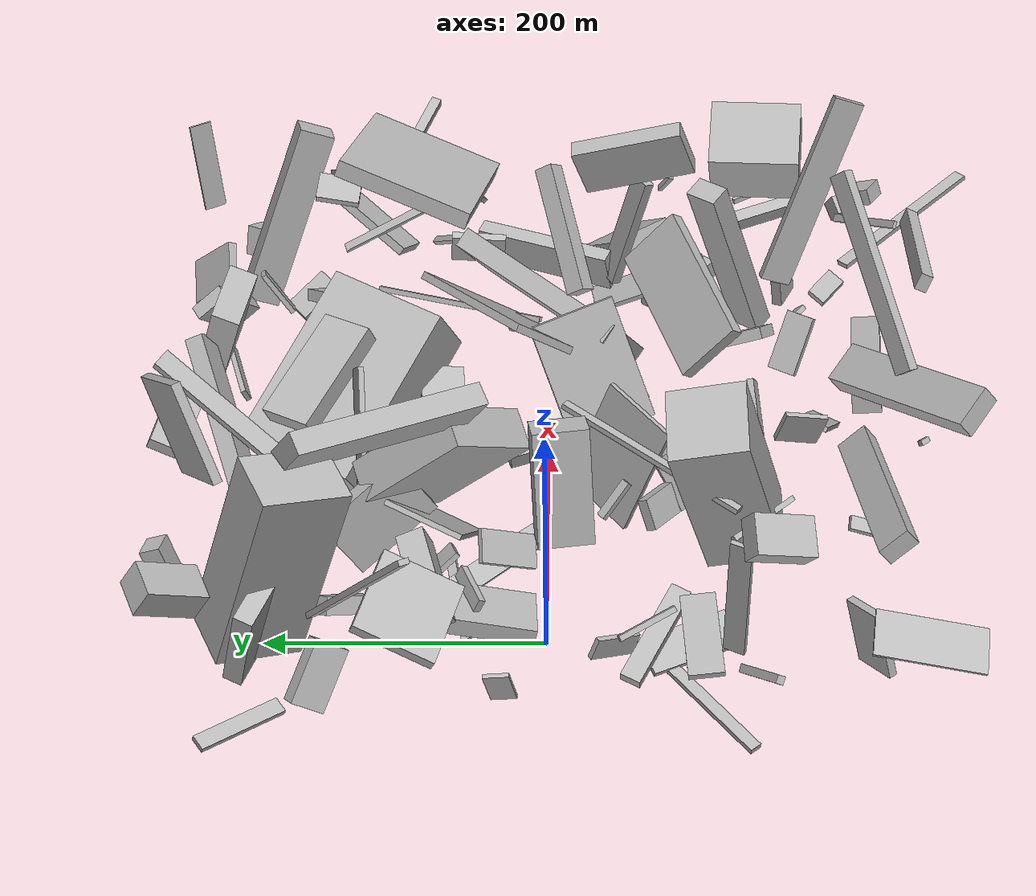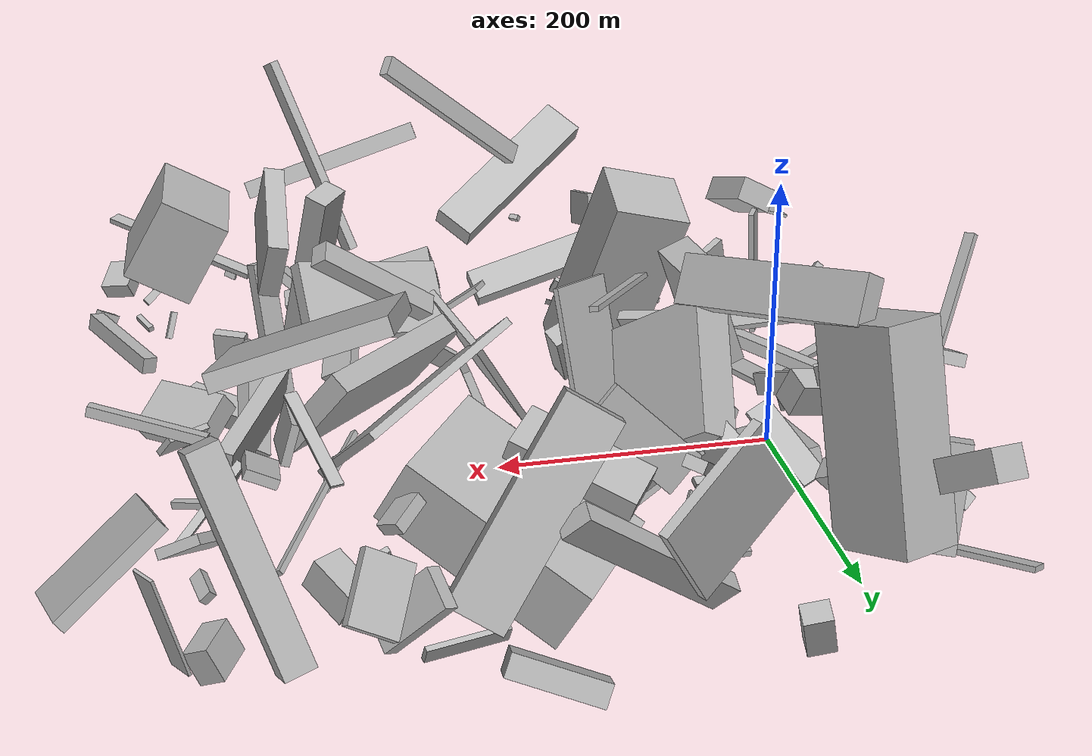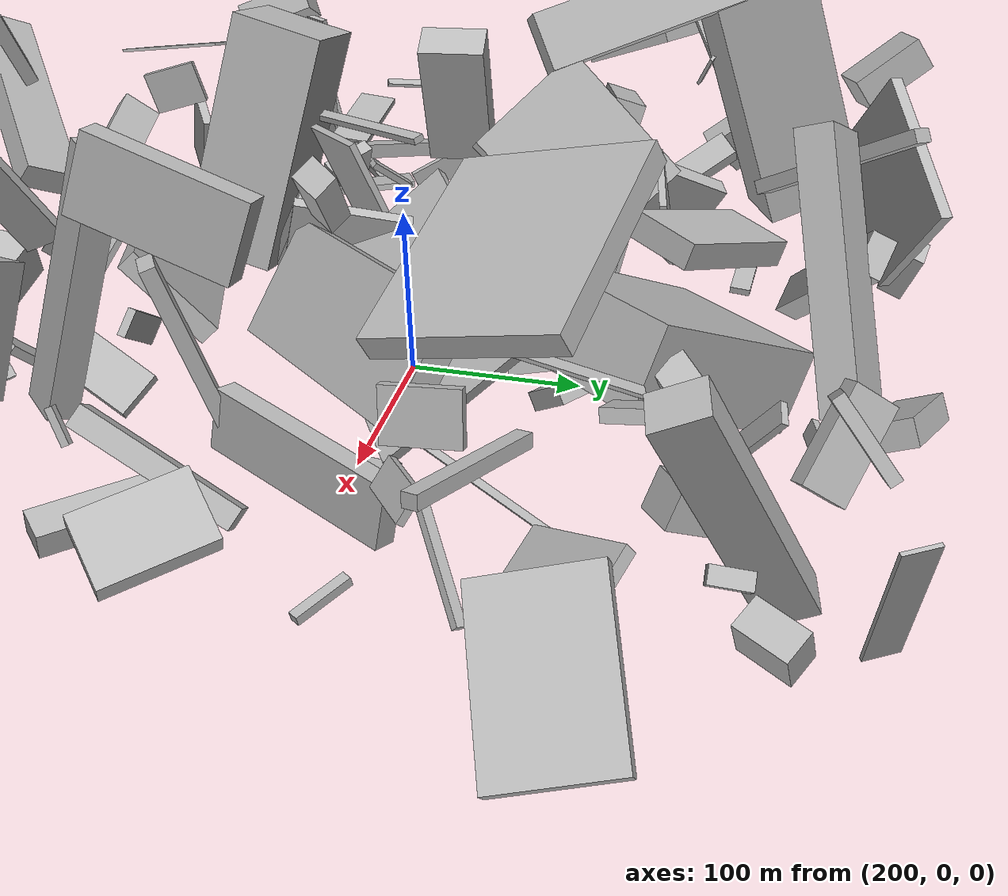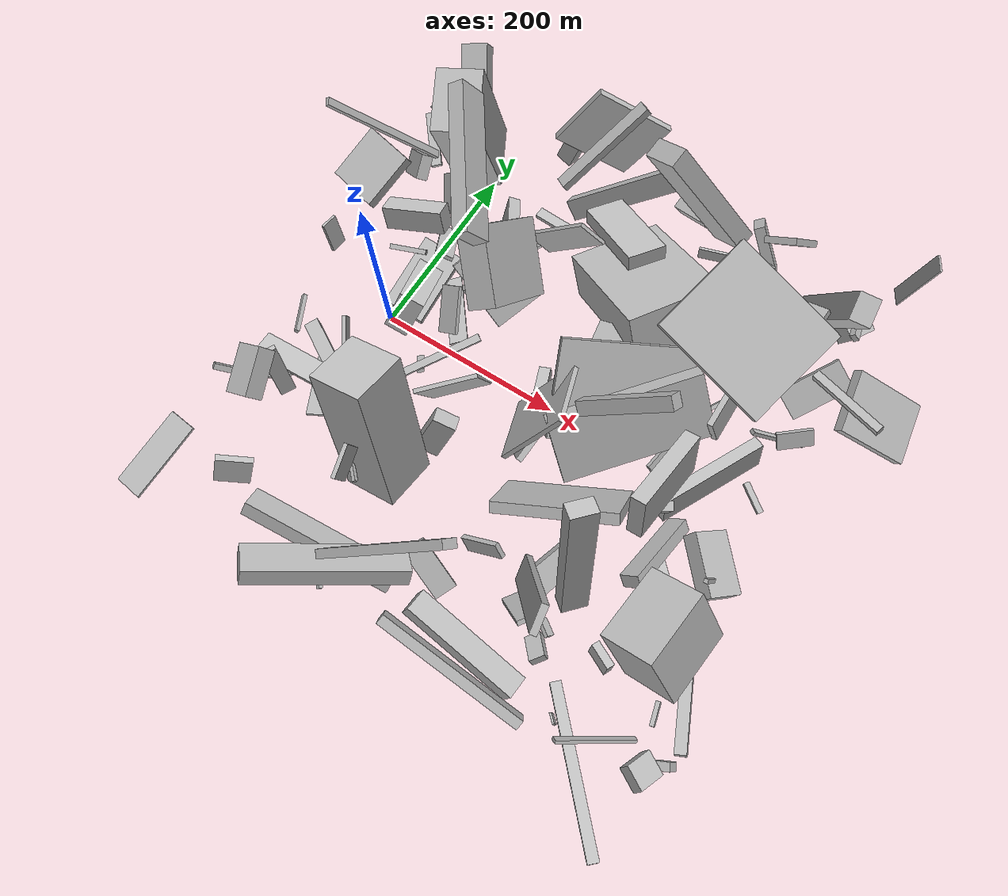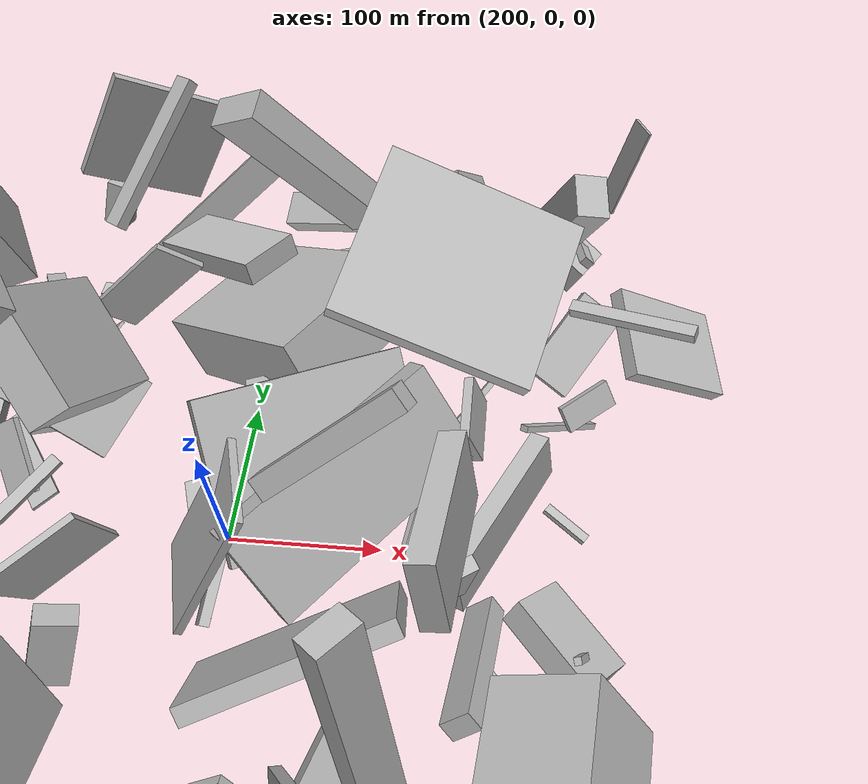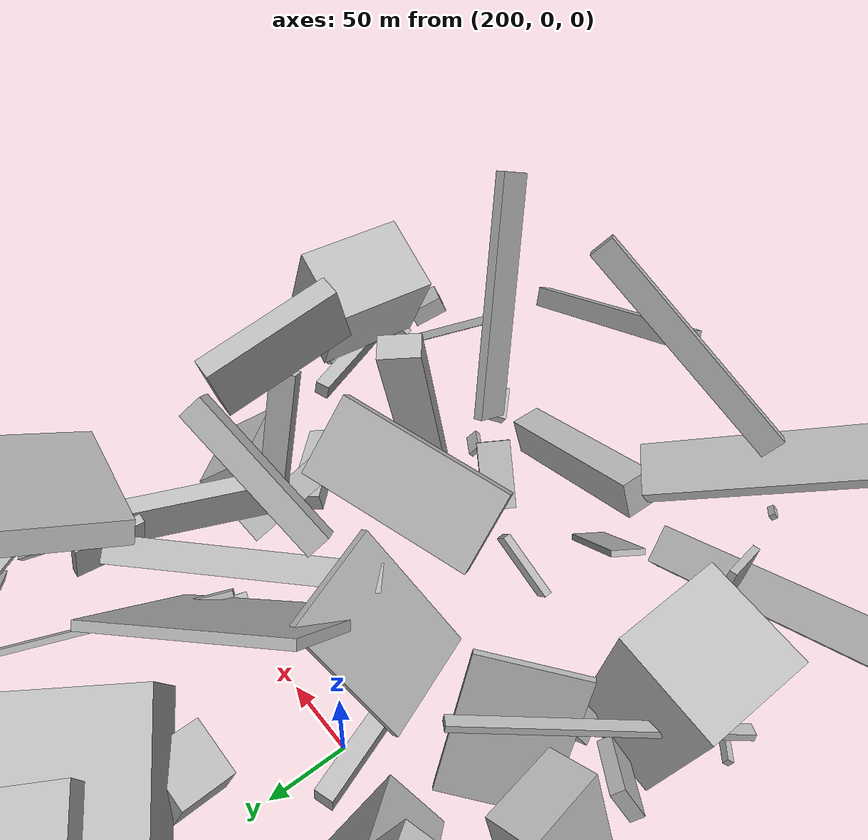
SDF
<sdf version="1.6">
 <world name="default">
  <scene>
   <sky><clouds><speed>12</speed></clouds></sky>
   <ambient>0.4 0.4 0.4 1</ambient>
   <background>0.7 0.7 0.7 1</background>
   <shadows>1</shadows>
  </scene>
  <gravity>0 0 -9.8066</gravity>
  <magnetic_field>6e-06 2.3e-05 -4.2e-05</magnetic_field>
  <physics default="0" name="default_physics" type="ode">
   <ode>
    <solver>
     <type>quick</type>
     <iters>10</iters>
     <sor>1.0</sor>
     <use_dynamic_moi_rescaling>0</use_dynamic_moi_rescaling>
    </solver>
    <constraints>
     <cfm>0</cfm>
     <erp>0.2</erp>
     <contact_max_correcting_vel>100</contact_max_correcting_vel>
     <contact_surface_layer>0.001</contact_surface_layer>
    </constraints>
   </ode>
   <max_step_size>0.004</max_step_size>
   <real_time_factor>1</real_time_factor>
   <real_time_update_rate>250</real_time_update_rate>
  </physics>
  <light name="sun" type="directional">
   <pose>0 0 10 0 0 0</pose>
   <diffuse>0.8 0.8 0.8 1</diffuse>
   <specular>0.2 0.2 0.2 1</specular>
   <attenuation>
    <range>1000</range>
    <constant>0.9</constant>
    <linear>0.01</linear>
    <quadratic>0.001</quadratic>
   </attenuation>
   <direction>-0.5 0.1 -0.9</direction>
  </light>
  <model name="building_1">
   <static>0</static>
   <pose>309.46362390081805 201.35652738300936 47.48775551985342 0.43576493843103864 0.506766276595603 1.9743907321214966</pose>
   <link name="link">
    <gravity>0</gravity>
    <pose>0 0 19.0 0 0 0</pose>
    <collision name="collision"><geometry><box><size>4 13 38</size></box></geometry></collision>
    <visual name="visual">
     <cast_shadows>0</cast_shadows>
     <geometry><box><size>4 13 38</size></box></geometry>
     <material>
      <script>
       <uri>model://HANNAS_wall/materials/scripts</uri>
       <uri>model://HANNAS_wall/materials/textures</uri>
       <name>vrc/HANNAS_wall</name>
      </script>
     </material>
    </visual>
   </link>
  </model>
  <model name="building_2">
   <static>0</static>
   <pose>-28.077921581289214 -135.4925500185197 135.75882159057304 1.965357414872305 -0.5212782521442816 0.08638813833298847</pose>
   <link name="link">
    <gravity>0</gravity>
    <pose>0 0 23.0 0 0 0</pose>
    <collision name="collision"><geometry><box><size>29 18 46</size></box></geometry></collision>
    <visual name="visual">
     <cast_shadows>0</cast_shadows>
     <geometry><box><size>29 18 46</size></box></geometry>
     <material>
      <script>
       <uri>model://HANNAS_wall/materials/scripts</uri>
       <uri>model://HANNAS_wall/materials/textures</uri>
       <name>vrc/HANNAS_wall</name>
      </script>
     </material>
    </visual>
   </link>
  </model>
  <model name="building_3">
   <static>0</static>
   <pose>211.67828912738628 155.78817886532025 68.08862332421445 3.128858214851699 -0.5135115431409025 -0.5868482593631186</pose>
   <link name="link">
    <gravity>0</gravity>
    <pose>0 0 24.5 0 0 0</pose>
    <collision name="collision"><geometry><box><size>142 99 49</size></box></geometry></collision>
    <visual name="visual">
     <cast_shadows>0</cast_shadows>
     <geometry><box><size>142 99 49</size></box></geometry>
     <material>
      <script>
       <uri>model://HANNAS_wall/materials/scripts</uri>
       <uri>model://HANNAS_wall/materials/textures</uri>
       <name>vrc/HANNAS_wall</name>
      </script>
     </material>
    </visual>
   </link>
  </model>
  <model name="building_4">
   <static>0</static>
   <pose>359.27400351940173 -121.61541307797461 53.61073402621936 2.182763491040047 0.6218465289626921 -2.8656768899968434</pose>
   <link name="link">
    <gravity>0</gravity>
    <pose>0 0 47.5 0 0 0</pose>
    <collision name="collision"><geometry><box><size>19 13 95</size></box></geometry></collision>
    <visual name="visual">
     <cast_shadows>0</cast_shadows>
     <geometry><box><size>19 13 95</size></box></geometry>
     <material>
      <script>
       <uri>model://HANNAS_wall/materials/scripts</uri>
       <uri>model://HANNAS_wall/materials/textures</uri>
       <name>vrc/HANNAS_wall</name>
      </script>
     </material>
    </visual>
   </link>
  </model>
  <model name="building_5">
   <static>0</static>
   <pose>84.2323748721512 82.61260588119646 39.636423034816204 0.7574015520571209 -0.22801859578492628 1.1823374553878339</pose>
   <link name="link">
    <gravity>0</gravity>
    <pose>0 0 2.0 0 0 0</pose>
    <collision name="collision"><geometry><box><size>60 82 4</size></box></geometry></collision>
    <visual name="visual">
     <cast_shadows>0</cast_shadows>
     <geometry><box><size>60 82 4</size></box></geometry>
     <material>
      <script>
       <uri>model://HANNAS_wall/materials/scripts</uri>
       <uri>model://HANNAS_wall/materials/textures</uri>
       <name>vrc/HANNAS_wall</name>
      </script>
     </material>
    </visual>
   </link>
  </model>
  <model name="building_6">
   <static>0</static>
   <pose>36.533790259864055 63.985927417758774 11.089640249159746 -3.049824708501027 -0.3883903565383661 -1.4268370130343577</pose>
   <link name="link">
    <gravity>0</gravity>
    <pose>0 0 2.0 0 0 0</pose>
    <collision name="collision"><geometry><box><size>7 80 4</size></box></geometry></collision>
    <visual name="visual">
     <cast_shadows>0</cast_shadows>
     <geometry><box><size>7 80 4</size></box></geometry>
     <material>
      <script>
       <uri>model://HANNAS_wall/materials/scripts</uri>
       <uri>model://HANNAS_wall/materials/textures</uri>
       <name>vrc/HANNAS_wall</name>
      </script>
     </material>
    </visual>
   </link>
  </model>
  <model name="building_7">
   <static>0</static>
   <pose>348.3013595316348 -232.51220273986084 62.30479469964007 -0.654387931315331 1.4542069693492485 -1.4633512062814251</pose>
   <link name="link">
    <gravity>0</gravity>
    <pose>0 0 72.0 0 0 0</pose>
    <collision name="collision"><geometry><box><size>4 10 144</size></box></geometry></collision>
    <visual name="visual">
     <cast_shadows>0</cast_shadows>
     <geometry><box><size>4 10 144</size></box></geometry>
     <material>
      <script>
       <uri>model://HANNAS_wall/materials/scripts</uri>
       <uri>model://HANNAS_wall/materials/textures</uri>
       <name>vrc/HANNAS_wall</name>
      </script>
     </material>
    </visual>
   </link>
  </model>
  <model name="building_8">
   <static>0</static>
   <pose>6.561336751795196 195.85633823105283 104.75732768667348 1.6594283061576993 0.28385549652941927 -1.0969756349459892</pose>
   <link name="link">
    <gravity>0</gravity>
    <pose>0 0 23.5 0 0 0</pose>
    <collision name="collision"><geometry><box><size>64 150 47</size></box></geometry></collision>
    <visual name="visual">
     <cast_shadows>0</cast_shadows>
     <geometry><box><size>64 150 47</size></box></geometry>
     <material>
      <script>
       <uri>model://HANNAS_wall/materials/scripts</uri>
       <uri>model://HANNAS_wall/materials/textures</uri>
       <name>vrc/HANNAS_wall</name>
      </script>
     </material>
    </visual>
   </link>
  </model>
  <model name="building_9">
   <static>0</static>
   <pose>319.9178127410755 -129.8583718795964 98.54489155091844 -1.1713281129779392 -1.259479159622659 2.0318326055238733</pose>
   <link name="link">
    <gravity>0</gravity>
    <pose>0 0 13.0 0 0 0</pose>
    <collision name="collision"><geometry><box><size>150 17 26</size></box></geometry></collision>
    <visual name="visual">
     <cast_shadows>0</cast_shadows>
     <geometry><box><size>150 17 26</size></box></geometry>
     <material>
      <script>
       <uri>model://HANNAS_wall/materials/scripts</uri>
       <uri>model://HANNAS_wall/materials/textures</uri>
       <name>vrc/HANNAS_wall</name>
      </script>
     </material>
    </visual>
   </link>
  </model>
  <model name="building_10">
   <static>0</static>
   <pose>316.39583741115655 62.48465080775631 57.22004347062631 -1.201629691936962 -0.7011251375763857 1.9411494548542612</pose>
   <link name="link">
    <gravity>0</gravity>
    <pose>0 0 68.0 0 0 0</pose>
    <collision name="collision"><geometry><box><size>98 6 136</size></box></geometry></collision>
    <visual name="visual">
     <cast_shadows>0</cast_shadows>
     <geometry><box><size>98 6 136</size></box></geometry>
     <material>
      <script>
       <uri>model://HANNAS_wall/materials/scripts</uri>
       <uri>model://HANNAS_wall/materials/textures</uri>
       <name>vrc/HANNAS_wall</name>
      </script>
     </material>
    </visual>
   </link>
  </model>
  <model name="building_11">
   <static>0</static>
   <pose>143.91724486819183 -31.254401568298526 72.23126482967791 1.7500805742641816 0.32054610094710945 -0.7633622267411793</pose>
   <link name="link">
    <gravity>0</gravity>
    <pose>0 0 30.5 0 0 0</pose>
    <collision name="collision"><geometry><box><size>4 90 61</size></box></geometry></collision>
    <visual name="visual">
     <cast_shadows>0</cast_shadows>
     <geometry><box><size>4 90 61</size></box></geometry>
     <material>
      <script>
       <uri>model://HANNAS_wall/materials/scripts</uri>
       <uri>model://HANNAS_wall/materials/textures</uri>
       <name>vrc/HANNAS_wall</name>
      </script>
     </material>
    </visual>
   </link>
  </model>
  <model name="building_12">
   <static>0</static>
   <pose>385.51148551328515 62.179323880258615 59.6660498435576 -2.2493902127419956 -0.413842254702614 -0.6548503010820251</pose>
   <link name="link">
    <gravity>0</gravity>
    <pose>0 0 35.0 0 0 0</pose>
    <collision name="collision"><geometry><box><size>6 4 70</size></box></geometry></collision>
    <visual name="visual">
     <cast_shadows>0</cast_shadows>
     <geometry><box><size>6 4 70</size></box></geometry>
     <material>
      <script>
       <uri>model://HANNAS_wall/materials/scripts</uri>
       <uri>model://HANNAS_wall/materials/textures</uri>
       <name>vrc/HANNAS_wall</name>
      </script>
     </material>
    </visual>
   </link>
  </model>
  <model name="building_13">
   <static>0</static>
   <pose>111.81549015365066 -127.25933531816918 90.60414349734894 2.418666830579016 1.2242428078256662 -0.7427514458721205</pose>
   <link name="link">
    <gravity>0</gravity>
    <pose>0 0 28.5 0 0 0</pose>
    <collision name="collision"><geometry><box><size>150 57 57</size></box></geometry></collision>
    <visual name="visual">
     <cast_shadows>0</cast_shadows>
     <geometry><box><size>150 57 57</size></box></geometry>
     <material>
      <script>
       <uri>model://HANNAS_wall/materials/scripts</uri>
       <uri>model://HANNAS_wall/materials/textures</uri>
       <name>vrc/HANNAS_wall</name>
      </script>
     </material>
    </visual>
   </link>
  </model>
  <model name="building_14">
   <static>0</static>
   <pose>264.49621758561995 -244.52331242339997 47.64009809487415 3.0064246165483777 0.28639670517796556 -0.1086999341273628</pose>
   <link name="link">
    <gravity>0</gravity>
    <pose>0 0 13.5 0 0 0</pose>
    <collision name="collision"><geometry><box><size>120 22 27</size></box></geometry></collision>
    <visual name="visual">
     <cast_shadows>0</cast_shadows>
     <geometry><box><size>120 22 27</size></box></geometry>
     <material>
      <script>
       <uri>model://HANNAS_wall/materials/scripts</uri>
       <uri>model://HANNAS_wall/materials/textures</uri>
       <name>vrc/HANNAS_wall</name>
      </script>
     </material>
    </visual>
   </link>
  </model>
  <model name="building_15">
   <static>0</static>
   <pose>371.9856344263977 -184.61784834907158 23.114268101412023 1.4476724623546866 -0.016943345255074002 -0.44664192721374096</pose>
   <link name="link">
    <gravity>0</gravity>
    <pose>0 0 4.0 0 0 0</pose>
    <collision name="collision"><geometry><box><size>25 23 8</size></box></geometry></collision>
    <visual name="visual">
     <cast_shadows>0</cast_shadows>
     <geometry><box><size>25 23 8</size></box></geometry>
     <material>
      <script>
       <uri>model://HANNAS_wall/materials/scripts</uri>
       <uri>model://HANNAS_wall/materials/textures</uri>
       <name>vrc/HANNAS_wall</name>
      </script>
     </material>
    </visual>
   </link>
  </model>
  <model name="building_16">
   <static>0</static>
   <pose>79.8772940960351 49.98719671121852 157.3199193407463 1.1898310206667864 -0.987084384476045 -2.212910500101704</pose>
   <link name="link">
    <gravity>0</gravity>
    <pose>0 0 75.0 0 0 0</pose>
    <collision name="collision"><geometry><box><size>35 17 150</size></box></geometry></collision>
    <visual name="visual">
     <cast_shadows>0</cast_shadows>
     <geometry><box><size>35 17 150</size></box></geometry>
     <material>
      <script>
       <uri>model://HANNAS_wall/materials/scripts</uri>
       <uri>model://HANNAS_wall/materials/textures</uri>
       <name>vrc/HANNAS_wall</name>
      </script>
     </material>
    </visual>
   </link>
  </model>
  <model name="building_17">
   <static>0</static>
   <pose>409.4886636101675 120.23899048069518 110.59745018672916 -0.6172711369329025 -1.3240112378763442 -2.879353847189306</pose>
   <link name="link">
    <gravity>0</gravity>
    <pose>0 0 39.0 0 0 0</pose>
    <collision name="collision"><geometry><box><size>7 8 78</size></box></geometry></collision>
    <visual name="visual">
     <cast_shadows>0</cast_shadows>
     <geometry><box><size>7 8 78</size></box></geometry>
     <material>
      <script>
       <uri>model://HANNAS_wall/materials/scripts</uri>
       <uri>model://HANNAS_wall/materials/textures</uri>
       <name>vrc/HANNAS_wall</name>
      </script>
     </material>
    </visual>
   </link>
  </model>
  <model name="building_18">
   <static>0</static>
   <pose>-61.48344934223279 -115.11963301348128 4.788785364855716 -3.1100774594400113 0.04659520486741724 -2.4701601331710745</pose>
   <link name="link">
    <gravity>0</gravity>
    <pose>0 0 2.0 0 0 0</pose>
    <collision name="collision"><geometry><box><size>89 9 4</size></box></geometry></collision>
    <visual name="visual">
     <cast_shadows>0</cast_shadows>
     <geometry><box><size>89 9 4</size></box></geometry>
     <material>
      <script>
       <uri>model://HANNAS_wall/materials/scripts</uri>
       <uri>model://HANNAS_wall/materials/textures</uri>
       <name>vrc/HANNAS_wall</name>
      </script>
     </material>
    </visual>
   </link>
  </model>
  <model name="building_19">
   <static>0</static>
   <pose>278.28148205647415 -171.71329424370396 103.8499662033756 -0.2710461245618236 0.407536978835516 -1.429517397415596</pose>
   <link name="link">
    <gravity>0</gravity>
    <pose>0 0 75.0 0 0 0</pose>
    <collision name="collision"><geometry><box><size>24 6 150</size></box></geometry></collision>
    <visual name="visual">
     <cast_shadows>0</cast_shadows>
     <geometry><box><size>24 6 150</size></box></geometry>
     <material>
      <script>
       <uri>model://HANNAS_wall/materials/scripts</uri>
       <uri>model://HANNAS_wall/materials/textures</uri>
       <name>vrc/HANNAS_wall</name>
      </script>
     </material>
    </visual>
   </link>
  </model>
  <model name="building_20">
   <static>0</static>
   <pose>-51.41890146870562 257.7032145688921 99.28291315216119 -0.5549988851052058 0.17744111944107552 -2.7232561852881036</pose>
   <link name="link">
    <gravity>0</gravity>
    <pose>0 0 11.0 0 0 0</pose>
    <collision name="collision"><geometry><box><size>28 48 22</size></box></geometry></collision>
    <visual name="visual">
     <cast_shadows>0</cast_shadows>
     <geometry><box><size>28 48 22</size></box></geometry>
     <material>
      <script>
       <uri>model://HANNAS_wall/materials/scripts</uri>
       <uri>model://HANNAS_wall/materials/textures</uri>
       <name>vrc/HANNAS_wall</name>
      </script>
     </material>
    </visual>
   </link>
  </model>
  <model name="building_21">
   <static>0</static>
   <pose>451.4439782812763 -244.2115901558669 52.279972661034776 1.1323295374493418 0.17108012139445933 -0.4919120338889486</pose>
   <link name="link">
    <gravity>0</gravity>
    <pose>0 0 13.0 0 0 0</pose>
    <collision name="collision"><geometry><box><size>23 13 26</size></box></geometry></collision>
    <visual name="visual">
     <cast_shadows>0</cast_shadows>
     <geometry><box><size>23 13 26</size></box></geometry>
     <material>
      <script>
       <uri>model://HANNAS_wall/materials/scripts</uri>
       <uri>model://HANNAS_wall/materials/textures</uri>
       <name>vrc/HANNAS_wall</name>
      </script>
     </material>
    </visual>
   </link>
  </model>
  <model name="building_22">
   <static>0</static>
   <pose>-41.05394015820243 158.03452582841686 74.45168271766735 0.6596051981112768 0.20255919383012458 -0.9841541207012039</pose>
   <link name="link">
    <gravity>0</gravity>
    <pose>0 0 75.0 0 0 0</pose>
    <collision name="collision"><geometry><box><size>8 4 150</size></box></geometry></collision>
    <visual name="visual">
     <cast_shadows>0</cast_shadows>
     <geometry><box><size>8 4 150</size></box></geometry>
     <material>
      <script>
       <uri>model://HANNAS_wall/materials/scripts</uri>
       <uri>model://HANNAS_wall/materials/textures</uri>
       <name>vrc/HANNAS_wall</name>
      </script>
     </material>
    </visual>
   </link>
  </model>
  <model name="building_23">
   <static>0</static>
   <pose>304.738003514838 180.11330503812655 67.74197069879854 0.7941231796602019 -0.9836617274225596 -0.0971532040179213</pose>
   <link name="link">
    <gravity>0</gravity>
    <pose>0 0 13.5 0 0 0</pose>
    <collision name="collision"><geometry><box><size>9 19 27</size></box></geometry></collision>
    <visual name="visual">
     <cast_shadows>0</cast_shadows>
     <geometry><box><size>9 19 27</size></box></geometry>
     <material>
      <script>
       <uri>model://HANNAS_wall/materials/scripts</uri>
       <uri>model://HANNAS_wall/materials/textures</uri>
       <name>vrc/HANNAS_wall</name>
      </script>
     </material>
    </visual>
   </link>
  </model>
  <model name="building_24">
   <static>0</static>
   <pose>324.21815395612686 12.365732566802015 12.207041580689348 -0.09423448038242056 0.6741194637701514 2.9214239972737244</pose>
   <link name="link">
    <gravity>0</gravity>
    <pose>0 0 5.0 0 0 0</pose>
    <collision name="collision"><geometry><box><size>4 39 10</size></box></geometry></collision>
    <visual name="visual">
     <cast_shadows>0</cast_shadows>
     <geometry><box><size>4 39 10</size></box></geometry>
     <material>
      <script>
       <uri>model://HANNAS_wall/materials/scripts</uri>
       <uri>model://HANNAS_wall/materials/textures</uri>
       <name>vrc/HANNAS_wall</name>
      </script>
     </material>
    </visual>
   </link>
  </model>
  <model name="building_25">
   <static>0</static>
   <pose>136.19732894643224 -255.7094216957205 135.92152051602005 0.8297968130050105 -0.2930569359316144 2.2362842596840484</pose>
   <link name="link">
    <gravity>0</gravity>
    <pose>0 0 75.0 0 0 0</pose>
    <collision name="collision"><geometry><box><size>8 15 150</size></box></geometry></collision>
    <visual name="visual">
     <cast_shadows>0</cast_shadows>
     <geometry><box><size>8 15 150</size></box></geometry>
     <material>
      <script>
       <uri>model://HANNAS_wall/materials/scripts</uri>
       <uri>model://HANNAS_wall/materials/textures</uri>
       <name>vrc/HANNAS_wall</name>
      </script>
     </material>
    </visual>
   </link>
  </model>
  <model name="building_26">
   <static>0</static>
   <pose>420.7405414484789 221.76137710201016 59.321164204675554 1.2840117380409617 -0.769377723093428 0.39981676286321555</pose>
   <link name="link">
    <gravity>0</gravity>
    <pose>0 0 10.5 0 0 0</pose>
    <collision name="collision"><geometry><box><size>6 9 21</size></box></geometry></collision>
    <visual name="visual">
     <cast_shadows>0</cast_shadows>
     <geometry><box><size>6 9 21</size></box></geometry>
     <material>
      <script>
       <uri>model://HANNAS_wall/materials/scripts</uri>
       <uri>model://HANNAS_wall/materials/textures</uri>
       <name>vrc/HANNAS_wall</name>
      </script>
     </material>
    </visual>
   </link>
  </model>
  <model name="building_27">
   <static>0</static>
   <pose>220.97745476137584 -123.30411942724339 79.01978659322693 -1.2050605881555982 -0.8408907638800656 -1.4605159921123112</pose>
   <link name="link">
    <gravity>0</gravity>
    <pose>0 0 58.5 0 0 0</pose>
    <collision name="collision"><geometry><box><size>55 11 117</size></box></geometry></collision>
    <visual name="visual">
     <cast_shadows>0</cast_shadows>
     <geometry><box><size>55 11 117</size></box></geometry>
     <material>
      <script>
       <uri>model://HANNAS_wall/materials/scripts</uri>
       <uri>model://HANNAS_wall/materials/textures</uri>
       <name>vrc/HANNAS_wall</name>
      </script>
     </material>
    </visual>
   </link>
  </model>
  <model name="building_28">
   <static>0</static>
   <pose>421.57073112992236 -166.402727282559 103.28045651975125 -0.5056196899823714 0.04414128287469829 1.463042192567351</pose>
   <link name="link">
    <gravity>0</gravity>
    <pose>0 0 32.5 0 0 0</pose>
    <collision name="collision"><geometry><box><size>70 52 65</size></box></geometry></collision>
    <visual name="visual">
     <cast_shadows>0</cast_shadows>
     <geometry><box><size>70 52 65</size></box></geometry>
     <material>
      <script>
       <uri>model://HANNAS_wall/materials/scripts</uri>
       <uri>model://HANNAS_wall/materials/textures</uri>
       <name>vrc/HANNAS_wall</name>
      </script>
     </material>
    </visual>
   </link>
  </model>
  <model name="building_29">
   <static>0</static>
   <pose>44.17034252287611 -134.387049823508 88.86126852118855 -0.9336676088320623 -1.306238775513758 -1.2248868489905937</pose>
   <link name="link">
    <gravity>0</gravity>
    <pose>0 0 75.0 0 0 0</pose>
    <collision name="collision"><geometry><box><size>4 7 150</size></box></geometry></collision>
    <visual name="visual">
     <cast_shadows>0</cast_shadows>
     <geometry><box><size>4 7 150</size></box></geometry>
     <material>
      <script>
       <uri>model://HANNAS_wall/materials/scripts</uri>
       <uri>model://HANNAS_wall/materials/textures</uri>
       <name>vrc/HANNAS_wall</name>
      </script>
     </material>
    </visual>
   </link>
  </model>
  <model name="building_30">
   <static>0</static>
   <pose>194.44684986697507 -204.1476284580889 32.55716649621175 0.6565446376368466 -0.15847734125363377 1.118498700576509</pose>
   <link name="link">
    <gravity>0</gravity>
    <pose>0 0 2.0 0 0 0</pose>
    <collision name="collision"><geometry><box><size>23 57 4</size></box></geometry></collision>
    <visual name="visual">
     <cast_shadows>0</cast_shadows>
     <geometry><box><size>23 57 4</size></box></geometry>
     <material>
      <script>
       <uri>model://HANNAS_wall/materials/scripts</uri>
       <uri>model://HANNAS_wall/materials/textures</uri>
       <name>vrc/HANNAS_wall</name>
      </script>
     </material>
    </visual>
   </link>
  </model>
  <model name="building_31">
   <static>0</static>
   <pose>98.03608983364143 -229.1678409043021 43.43308630904886 0.35827753093758274 -0.8461940479167904 1.398403617816241</pose>
   <link name="link">
    <gravity>0</gravity>
    <pose>0 0 12.5 0 0 0</pose>
    <collision name="collision"><geometry><box><size>14 150 25</size></box></geometry></collision>
    <visual name="visual">
     <cast_shadows>0</cast_shadows>
     <geometry><box><size>14 150 25</size></box></geometry>
     <material>
      <script>
       <uri>model://HANNAS_wall/materials/scripts</uri>
       <uri>model://HANNAS_wall/materials/textures</uri>
       <name>vrc/HANNAS_wall</name>
      </script>
     </material>
    </visual>
   </link>
  </model>
  <model name="building_32">
   <static>0</static>
   <pose>99.51091329492351 -178.82337924328027 118.16177823151321 1.8759055209213944 -1.2815974727619508 -1.683761479937699</pose>
   <link name="link">
    <gravity>0</gravity>
    <pose>0 0 2.0 0 0 0</pose>
    <collision name="collision"><geometry><box><size>25 32 4</size></box></geometry></collision>
    <visual name="visual">
     <cast_shadows>0</cast_shadows>
     <geometry><box><size>25 32 4</size></box></geometry>
     <material>
      <script>
       <uri>model://HANNAS_wall/materials/scripts</uri>
       <uri>model://HANNAS_wall/materials/textures</uri>
       <name>vrc/HANNAS_wall</name>
      </script>
     </material>
    </visual>
   </link>
  </model>
  <model name="building_33">
   <static>0</static>
   <pose>222.95859791907768 -161.35242033915432 21.218085980553944 -1.9986892932430358 0.85907340463808 -0.40217064702903527</pose>
   <link name="link">
    <gravity>0</gravity>
    <pose>0 0 2.5 0 0 0</pose>
    <collision name="collision"><geometry><box><size>17 46 5</size></box></geometry></collision>
    <visual name="visual">
     <cast_shadows>0</cast_shadows>
     <geometry><box><size>17 46 5</size></box></geometry>
     <material>
      <script>
       <uri>model://HANNAS_wall/materials/scripts</uri>
       <uri>model://HANNAS_wall/materials/textures</uri>
       <name>vrc/HANNAS_wall</name>
      </script>
     </material>
    </visual>
   </link>
  </model>
  <model name="building_34">
   <static>0</static>
   <pose>417.29273005530035 22.91178297883453 12.531775327448083 -2.9493783547742725 -0.013909598977437296 0.9687678245279114</pose>
   <link name="link">
    <gravity>0</gravity>
    <pose>0 0 2.5 0 0 0</pose>
    <collision name="collision"><geometry><box><size>6 32 5</size></box></geometry></collision>
    <visual name="visual">
     <cast_shadows>0</cast_shadows>
     <geometry><box><size>6 32 5</size></box></geometry>
     <material>
      <script>
       <uri>model://HANNAS_wall/materials/scripts</uri>
       <uri>model://HANNAS_wall/materials/textures</uri>
       <name>vrc/HANNAS_wall</name>
      </script>
     </material>
    </visual>
   </link>
  </model>
  <model name="building_35">
   <static>0</static>
   <pose>435.0642640277096 -85.42450491516668 29.33039933083458 1.3902258920466453 0.9651706859474911 -2.5467349887934896</pose>
   <link name="link">
    <gravity>0</gravity>
    <pose>0 0 30.5 0 0 0</pose>
    <collision name="collision"><geometry><box><size>17 40 61</size></box></geometry></collision>
    <visual name="visual">
     <cast_shadows>0</cast_shadows>
     <geometry><box><size>17 40 61</size></box></geometry>
     <material>
      <script>
       <uri>model://HANNAS_wall/materials/scripts</uri>
       <uri>model://HANNAS_wall/materials/textures</uri>
       <name>vrc/HANNAS_wall</name>
      </script>
     </material>
    </visual>
   </link>
  </model>
  <model name="building_36">
   <static>0</static>
   <pose>-39.82207419633159 81.04194851132804 115.78637293248654 -1.7730047206557609 -0.4029775703085149 1.3480885039355262</pose>
   <link name="link">
    <gravity>0</gravity>
    <pose>0 0 31.0 0 0 0</pose>
    <collision name="collision"><geometry><box><size>59 9 62</size></box></geometry></collision>
    <visual name="visual">
     <cast_shadows>0</cast_shadows>
     <geometry><box><size>59 9 62</size></box></geometry>
     <material>
      <script>
       <uri>model://HANNAS_wall/materials/scripts</uri>
       <uri>model://HANNAS_wall/materials/textures</uri>
       <name>vrc/HANNAS_wall</name>
      </script>
     </material>
    </visual>
   </link>
  </model>
  <model name="building_37">
   <static>0</static>
   <pose>-62.67924427500042 207.12646594694317 60.603325832311675 1.4827586129663017 -0.24392767413993338 1.2305515022820621</pose>
   <link name="link">
    <gravity>0</gravity>
    <pose>0 0 19.5 0 0 0</pose>
    <collision name="collision"><geometry><box><size>14 75 39</size></box></geometry></collision>
    <visual name="visual">
     <cast_shadows>0</cast_shadows>
     <geometry><box><size>14 75 39</size></box></geometry>
     <material>
      <script>
       <uri>model://HANNAS_wall/materials/scripts</uri>
       <uri>model://HANNAS_wall/materials/textures</uri>
       <name>vrc/HANNAS_wall</name>
      </script>
     </material>
    </visual>
   </link>
  </model>
  <model name="building_38">
   <static>0</static>
   <pose>53.72161583813893 -30.469177152015778 108.9632053507379 -1.580017883568845 -1.2314335869569053 0.14933126224363016</pose>
   <link name="link">
    <gravity>0</gravity>
    <pose>0 0 20.0 0 0 0</pose>
    <collision name="collision"><geometry><box><size>87 24 40</size></box></geometry></collision>
    <visual name="visual">
     <cast_shadows>0</cast_shadows>
     <geometry><box><size>87 24 40</size></box></geometry>
     <material>
      <script>
       <uri>model://HANNAS_wall/materials/scripts</uri>
       <uri>model://HANNAS_wall/materials/textures</uri>
       <name>vrc/HANNAS_wall</name>
      </script>
     </material>
    </visual>
   </link>
  </model>
  <model name="building_39">
   <static>0</static>
   <pose>61.16653620594562 -70.74318692677993 66.99017246951475 -1.9673699610208624 0.9998672512027429 -2.5435271077006636</pose>
   <link name="link">
    <gravity>0</gravity>
    <pose>0 0 16.0 0 0 0</pose>
    <collision name="collision"><geometry><box><size>23 8 32</size></box></geometry></collision>
    <visual name="visual">
     <cast_shadows>0</cast_shadows>
     <geometry><box><size>23 8 32</size></box></geometry>
     <material>
      <script>
       <uri>model://HANNAS_wall/materials/scripts</uri>
       <uri>model://HANNAS_wall/materials/textures</uri>
       <name>vrc/HANNAS_wall</name>
      </script>
     </material>
    </visual>
   </link>
  </model>
  <model name="building_40">
   <static>0</static>
   <pose>106.09864096796497 -242.8547290196711 21.047245204429384 -0.48326042141245484 -0.3757318316316515 -0.2551385772194624</pose>
   <link name="link">
    <gravity>0</gravity>
    <pose>0 0 7.5 0 0 0</pose>
    <collision name="collision"><geometry><box><size>4 4 15</size></box></geometry></collision>
    <visual name="visual">
     <cast_shadows>0</cast_shadows>
     <geometry><box><size>4 4 15</size></box></geometry>
     <material>
      <script>
       <uri>model://HANNAS_wall/materials/scripts</uri>
       <uri>model://HANNAS_wall/materials/textures</uri>
       <name>vrc/HANNAS_wall</name>
      </script>
     </material>
    </visual>
   </link>
  </model>
  <model name="building_41">
   <static>0</static>
   <pose>-23.05304612374904 -123.69658281291171 75.14096751180298 1.304706251562262 -1.5203989616074607 -0.21420757760808043</pose>
   <link name="link">
    <gravity>0</gravity>
    <pose>0 0 8.0 0 0 0</pose>
    <collision name="collision"><geometry><box><size>98 4 16</size></box></geometry></collision>
    <visual name="visual">
     <cast_shadows>0</cast_shadows>
     <geometry><box><size>98 4 16</size></box></geometry>
     <material>
      <script>
       <uri>model://HANNAS_wall/materials/scripts</uri>
       <uri>model://HANNAS_wall/materials/textures</uri>
       <name>vrc/HANNAS_wall</name>
      </script>
     </material>
    </visual>
   </link>
  </model>
  <model name="building_42">
   <static>0</static>
   <pose>190.72321018270034 -220.43495022990737 93.0955015418593 1.1556386449002167 -0.48331315424283233 -0.720578385249718</pose>
   <link name="link">
    <gravity>0</gravity>
    <pose>0 0 70.5 0 0 0</pose>
    <collision name="collision"><geometry><box><size>32 16 141</size></box></geometry></collision>
    <visual name="visual">
     <cast_shadows>0</cast_shadows>
     <geometry><box><size>32 16 141</size></box></geometry>
     <material>
      <script>
       <uri>model://HANNAS_wall/materials/scripts</uri>
       <uri>model://HANNAS_wall/materials/textures</uri>
       <name>vrc/HANNAS_wall</name>
      </script>
     </material>
    </visual>
   </link>
  </model>
  <model name="building_43">
   <static>0</static>
   <pose>278.47495943842875 -272.79881396623904 135.98663534047122 -1.9486189094106698 -0.3117445863660129 3.098020665418793</pose>
   <link name="link">
    <gravity>0</gravity>
    <pose>0 0 4.5 0 0 0</pose>
    <collision name="collision"><geometry><box><size>139 13 9</size></box></geometry></collision>
    <visual name="visual">
     <cast_shadows>0</cast_shadows>
     <geometry><box><size>139 13 9</size></box></geometry>
     <material>
      <script>
       <uri>model://HANNAS_wall/materials/scripts</uri>
       <uri>model://HANNAS_wall/materials/textures</uri>
       <name>vrc/HANNAS_wall</name>
      </script>
     </material>
    </visual>
   </link>
  </model>
  <model name="building_44">
   <static>0</static>
   <pose>353.75257113213337 77.10459535437823 76.96102128623212 -1.8045874940755202 -1.2650101131542568 -2.9171897401226636</pose>
   <link name="link">
    <gravity>0</gravity>
    <pose>0 0 21.0 0 0 0</pose>
    <collision name="collision"><geometry><box><size>30 6 42</size></box></geometry></collision>
    <visual name="visual">
     <cast_shadows>0</cast_shadows>
     <geometry><box><size>30 6 42</size></box></geometry>
     <material>
      <script>
       <uri>model://HANNAS_wall/materials/scripts</uri>
       <uri>model://HANNAS_wall/materials/textures</uri>
       <name>vrc/HANNAS_wall</name>
      </script>
     </material>
    </visual>
   </link>
  </model>
  <model name="building_45">
   <static>0</static>
   <pose>284.80275784662217 -6.012684874198516 144.15392835366106 -0.7570389780355352 0.6350587551150729 -2.831908424178896</pose>
   <link name="link">
    <gravity>0</gravity>
    <pose>0 0 7.5 0 0 0</pose>
    <collision name="collision"><geometry><box><size>99 14 15</size></box></geometry></collision>
    <visual name="visual">
     <cast_shadows>0</cast_shadows>
     <geometry><box><size>99 14 15</size></box></geometry>
     <material>
      <script>
       <uri>model://HANNAS_wall/materials/scripts</uri>
       <uri>model://HANNAS_wall/materials/textures</uri>
       <name>vrc/HANNAS_wall</name>
      </script>
     </material>
    </visual>
   </link>
  </model>
  <model name="building_46">
   <static>0</static>
   <pose>54.29535669258168 147.51158724097013 42.05963039511562 0.4828492368991201 -1.0205515827937879 1.5789459595811315</pose>
   <link name="link">
    <gravity>0</gravity>
    <pose>0 0 35.5 0 0 0</pose>
    <collision name="collision"><geometry><box><size>52 12 71</size></box></geometry></collision>
    <visual name="visual">
     <cast_shadows>0</cast_shadows>
     <geometry><box><size>52 12 71</size></box></geometry>
     <material>
      <script>
       <uri>model://HANNAS_wall/materials/scripts</uri>
       <uri>model://HANNAS_wall/materials/textures</uri>
       <name>vrc/HANNAS_wall</name>
      </script>
     </material>
    </visual>
   </link>
  </model>
  <model name="building_47">
   <static>0</static>
   <pose>393.61168876020884 223.39231105958083 81.87107444291938 2.5748658122032033 -1.0926442467079471 -0.8256321600432848</pose>
   <link name="link">
    <gravity>0</gravity>
    <pose>0 0 14.0 0 0 0</pose>
    <collision name="collision"><geometry><box><size>150 22 28</size></box></geometry></collision>
    <visual name="visual">
     <cast_shadows>0</cast_shadows>
     <geometry><box><size>150 22 28</size></box></geometry>
     <material>
      <script>
       <uri>model://HANNAS_wall/materials/scripts</uri>
       <uri>model://HANNAS_wall/materials/textures</uri>
       <name>vrc/HANNAS_wall</name>
      </script>
     </material>
    </visual>
   </link>
  </model>
  <model name="building_48">
   <static>0</static>
   <pose>334.0310264785058 187.46232418129887 43.44139068615005 3.067728603372716 0.4645263409933384 2.215627900442582</pose>
   <link name="link">
    <gravity>0</gravity>
    <pose>0 0 11.5 0 0 0</pose>
    <collision name="collision"><geometry><box><size>36 23 23</size></box></geometry></collision>
    <visual name="visual">
     <cast_shadows>0</cast_shadows>
     <geometry><box><size>36 23 23</size></box></geometry>
     <material>
      <script>
       <uri>model://HANNAS_wall/materials/scripts</uri>
       <uri>model://HANNAS_wall/materials/textures</uri>
       <name>vrc/HANNAS_wall</name>
      </script>
     </material>
    </visual>
   </link>
  </model>
  <model name="building_49">
   <static>0</static>
   <pose>124.58424795564548 -85.32057700942784 40.150795754069705 1.1745858687902657 0.3873456016805238 0.2314890029302911</pose>
   <link name="link">
    <gravity>0</gravity>
    <pose>0 0 8.5 0 0 0</pose>
    <collision name="collision"><geometry><box><size>24 46 17</size></box></geometry></collision>
    <visual name="visual">
     <cast_shadows>0</cast_shadows>
     <geometry><box><size>24 46 17</size></box></geometry>
     <material>
      <script>
       <uri>model://HANNAS_wall/materials/scripts</uri>
       <uri>model://HANNAS_wall/materials/textures</uri>
       <name>vrc/HANNAS_wall</name>
      </script>
     </material>
    </visual>
   </link>
  </model>
  <model name="building_50">
   <static>0</static>
   <pose>246.98811151247773 107.5499189951752 30.211697980508887 3.0939970801669077 0.9781684153351085 0.918383842802471</pose>
   <link name="link">
    <gravity>0</gravity>
    <pose>0 0 13.5 0 0 0</pose>
    <collision name="collision"><geometry><box><size>11 23 27</size></box></geometry></collision>
    <visual name="visual">
     <cast_shadows>0</cast_shadows>
     <geometry><box><size>11 23 27</size></box></geometry>
     <material>
      <script>
       <uri>model://HANNAS_wall/materials/scripts</uri>
       <uri>model://HANNAS_wall/materials/textures</uri>
       <name>vrc/HANNAS_wall</name>
      </script>
     </material>
    </visual>
   </link>
  </model>
  <model name="building_51">
   <static>0</static>
   <pose>415.40748344861305 233.39112325798635 17.18062067894897 -0.408704491964975 -0.12025387853727165 -2.087684509227728</pose>
   <link name="link">
    <gravity>0</gravity>
    <pose>0 0 12.0 0 0 0</pose>
    <collision name="collision"><geometry><box><size>30 18 24</size></box></geometry></collision>
    <visual name="visual">
     <cast_shadows>0</cast_shadows>
     <geometry><box><size>30 18 24</size></box></geometry>
     <material>
      <script>
       <uri>model://HANNAS_wall/materials/scripts</uri>
       <uri>model://HANNAS_wall/materials/textures</uri>
       <name>vrc/HANNAS_wall</name>
      </script>
     </material>
    </visual>
   </link>
  </model>
  <model name="building_52">
   <static>0</static>
   <pose>-18.395672278974978 -46.34359116153328 20.719452880238087 1.6431789307445022 -1.188237107638643 -1.084975366499897</pose>
   <link name="link">
    <gravity>0</gravity>
    <pose>0 0 2.0 0 0 0</pose>
    <collision name="collision"><geometry><box><size>17 37 4</size></box></geometry></collision>
    <visual name="visual">
     <cast_shadows>0</cast_shadows>
     <geometry><box><size>17 37 4</size></box></geometry>
     <material>
      <script>
       <uri>model://HANNAS_wall/materials/scripts</uri>
       <uri>model://HANNAS_wall/materials/textures</uri>
       <name>vrc/HANNAS_wall</name>
      </script>
     </material>
    </visual>
   </link>
  </model>
  <model name="building_53">
   <static>0</static>
   <pose>-19.101014820206856 -227.87569010796057 30.371800531066896 1.6411951338758597 -0.31110380445166563 -2.5634798788783977</pose>
   <link name="link">
    <gravity>0</gravity>
    <pose>0 0 3.0 0 0 0</pose>
    <collision name="collision"><geometry><box><size>35 51 6</size></box></geometry></collision>
    <visual name="visual">
     <cast_shadows>0</cast_shadows>
     <geometry><box><size>35 51 6</size></box></geometry>
     <material>
      <script>
       <uri>model://HANNAS_wall/materials/scripts</uri>
       <uri>model://HANNAS_wall/materials/textures</uri>
       <name>vrc/HANNAS_wall</name>
      </script>
     </material>
    </visual>
   </link>
  </model>
  <model name="building_54">
   <static>0</static>
   <pose>447.39536191367364 133.72383619271608 71.95958108905215 -2.1980076276316844 0.22523781184431688 -1.3897981237188317</pose>
   <link name="link">
    <gravity>0</gravity>
    <pose>0 0 44.0 0 0 0</pose>
    <collision name="collision"><geometry><box><size>62 10 88</size></box></geometry></collision>
    <visual name="visual">
     <cast_shadows>0</cast_shadows>
     <geometry><box><size>62 10 88</size></box></geometry>
     <material>
      <script>
       <uri>model://HANNAS_wall/materials/scripts</uri>
       <uri>model://HANNAS_wall/materials/textures</uri>
       <name>vrc/HANNAS_wall</name>
      </script>
     </material>
    </visual>
   </link>
  </model>
  <model name="building_55">
   <static>0</static>
   <pose>145.2766642264788 189.37162474569294 78.75276900728825 -1.2201866854188745 -0.12606314348779657 -2.157175782238382</pose>
   <link name="link">
    <gravity>0</gravity>
    <pose>0 0 44.5 0 0 0</pose>
    <collision name="collision"><geometry><box><size>41 15 89</size></box></geometry></collision>
    <visual name="visual">
     <cast_shadows>0</cast_shadows>
     <geometry><box><size>41 15 89</size></box></geometry>
     <material>
      <script>
       <uri>model://HANNAS_wall/materials/scripts</uri>
       <uri>model://HANNAS_wall/materials/textures</uri>
       <name>vrc/HANNAS_wall</name>
      </script>
     </material>
    </visual>
   </link>
  </model>
  <model name="building_56">
   <static>0</static>
   <pose>435.67925834151583 -221.82409053101406 75.5995149604561 1.2510732628540449 -1.235448662244879 -2.58537083395274</pose>
   <link name="link">
    <gravity>0</gravity>
    <pose>0 0 10.5 0 0 0</pose>
    <collision name="collision"><geometry><box><size>4 4 21</size></box></geometry></collision>
    <visual name="visual">
     <cast_shadows>0</cast_shadows>
     <geometry><box><size>4 4 21</size></box></geometry>
     <material>
      <script>
       <uri>model://HANNAS_wall/materials/scripts</uri>
       <uri>model://HANNAS_wall/materials/textures</uri>
       <name>vrc/HANNAS_wall</name>
      </script>
     </material>
    </visual>
   </link>
  </model>
  <model name="building_57">
   <static>0</static>
   <pose>-48.852724114038494 -69.50383931305394 71.57277848196638 -0.7272457403825164 -0.15564486514129966 -1.0559307587692006</pose>
   <link name="link">
    <gravity>0</gravity>
    <pose>0 0 2.0 0 0 0</pose>
    <collision name="collision"><geometry><box><size>44 4 4</size></box></geometry></collision>
    <visual name="visual">
     <cast_shadows>0</cast_shadows>
     <geometry><box><size>44 4 4</size></box></geometry>
     <material>
      <script>
       <uri>model://HANNAS_wall/materials/scripts</uri>
       <uri>model://HANNAS_wall/materials/textures</uri>
       <name>vrc/HANNAS_wall</name>
      </script>
     </material>
    </visual>
   </link>
  </model>
  <model name="building_58">
   <static>0</static>
   <pose>151.75012412018708 241.09419197223454 58.197257912334216 0.9738632309772239 0.735483131621185 -0.3975750135415935</pose>
   <link name="link">
    <gravity>0</gravity>
    <pose>0 0 7.0 0 0 0</pose>
    <collision name="collision"><geometry><box><size>23 150 14</size></box></geometry></collision>
    <visual name="visual">
     <cast_shadows>0</cast_shadows>
     <geometry><box><size>23 150 14</size></box></geometry>
     <material>
      <script>
       <uri>model://HANNAS_wall/materials/scripts</uri>
       <uri>model://HANNAS_wall/materials/textures</uri>
       <name>vrc/HANNAS_wall</name>
      </script>
     </material>
    </visual>
   </link>
  </model>
  <model name="building_59">
   <static>0</static>
   <pose>287.56856198991227 -191.0329350182154 32.06704044113597 0.852179603677927 -0.06756857890048036 -2.164920205813818</pose>
   <link name="link">
    <gravity>0</gravity>
    <pose>0 0 2.5 0 0 0</pose>
    <collision name="collision"><geometry><box><size>23 47 5</size></box></geometry></collision>
    <visual name="visual">
     <cast_shadows>0</cast_shadows>
     <geometry><box><size>23 47 5</size></box></geometry>
     <material>
      <script>
       <uri>model://HANNAS_wall/materials/scripts</uri>
       <uri>model://HANNAS_wall/materials/textures</uri>
       <name>vrc/HANNAS_wall</name>
      </script>
     </material>
    </visual>
   </link>
  </model>
  <model name="building_60">
   <static>0</static>
   <pose>117.00743041213224 50.34973912160767 71.7280157701172 0.7111129139356057 -0.7570511030923963 -1.7340530133190504</pose>
   <link name="link">
    <gravity>0</gravity>
    <pose>0 0 39.5 0 0 0</pose>
    <collision name="collision"><geometry><box><size>95 31 79</size></box></geometry></collision>
    <visual name="visual">
     <cast_shadows>0</cast_shadows>
     <geometry><box><size>95 31 79</size></box></geometry>
     <material>
      <script>
       <uri>model://HANNAS_wall/materials/scripts</uri>
       <uri>model://HANNAS_wall/materials/textures</uri>
       <name>vrc/HANNAS_wall</name>
      </script>
     </material>
    </visual>
   </link>
  </model>
  <model name="building_61">
   <static>0</static>
   <pose>204.7642314358759 -69.83573403065903 29.37104500480845 -1.2322134432573884 0.344343416448662 0.010025877184712819</pose>
   <link name="link">
    <gravity>0</gravity>
    <pose>0 0 20.0 0 0 0</pose>
    <collision name="collision"><geometry><box><size>6 38 40</size></box></geometry></collision>
    <visual name="visual">
     <cast_shadows>0</cast_shadows>
     <geometry><box><size>6 38 40</size></box></geometry>
     <material>
      <script>
       <uri>model://HANNAS_wall/materials/scripts</uri>
       <uri>model://HANNAS_wall/materials/textures</uri>
       <name>vrc/HANNAS_wall</name>
      </script>
     </material>
    </visual>
   </link>
  </model>
  <model name="building_62">
   <static>0</static>
   <pose>197.10087984985495 -2.4903857087845056 66.3985280145477 1.1617559215148296 -0.9761515540645398 0.659556476393523</pose>
   <link name="link">
    <gravity>0</gravity>
    <pose>0 0 33.0 0 0 0</pose>
    <collision name="collision"><geometry><box><size>96 5 66</size></box></geometry></collision>
    <visual name="visual">
     <cast_shadows>0</cast_shadows>
     <geometry><box><size>96 5 66</size></box></geometry>
     <material>
      <script>
       <uri>model://HANNAS_wall/materials/scripts</uri>
       <uri>model://HANNAS_wall/materials/textures</uri>
       <name>vrc/HANNAS_wall</name>
      </script>
     </material>
    </visual>
   </link>
  </model>
  <model name="building_63">
   <static>0</static>
   <pose>129.47358827973528 -274.1540090940561 72.48914500945732 0.10683561030248093 0.7225161827199938 0.7967552269716598</pose>
   <link name="link">
    <gravity>0</gravity>
    <pose>0 0 2.0 0 0 0</pose>
    <collision name="collision"><geometry><box><size>4 8 4</size></box></geometry></collision>
    <visual name="visual">
     <cast_shadows>0</cast_shadows>
     <geometry><box><size>4 8 4</size></box></geometry>
     <material>
      <script>
       <uri>model://HANNAS_wall/materials/scripts</uri>
       <uri>model://HANNAS_wall/materials/textures</uri>
       <name>vrc/HANNAS_wall</name>
      </script>
     </material>
    </visual>
   </link>
  </model>
  <model name="building_64">
   <static>0</static>
   <pose>349.87614661018023 -23.65503466333881 156.52186145321934 0.5793719680858855 1.21932601398018 -1.0513948202108727</pose>
   <link name="link">
    <gravity>0</gravity>
    <pose>0 0 43.0 0 0 0</pose>
    <collision name="collision"><geometry><box><size>43 14 86</size></box></geometry></collision>
    <visual name="visual">
     <cast_shadows>0</cast_shadows>
     <geometry><box><size>43 14 86</size></box></geometry>
     <material>
      <script>
       <uri>model://HANNAS_wall/materials/scripts</uri>
       <uri>model://HANNAS_wall/materials/textures</uri>
       <name>vrc/HANNAS_wall</name>
      </script>
     </material>
    </visual>
   </link>
  </model>
  <model name="building_65">
   <static>0</static>
   <pose>225.0116493211129 229.70889445980606 101.81156068992402 0.9635966097710222 -0.9494512501993817 -2.7802450249950637</pose>
   <link name="link">
    <gravity>0</gravity>
    <pose>0 0 10.5 0 0 0</pose>
    <collision name="collision"><geometry><box><size>147 40 21</size></box></geometry></collision>
    <visual name="visual">
     <cast_shadows>0</cast_shadows>
     <geometry><box><size>147 40 21</size></box></geometry>
     <material>
      <script>
       <uri>model://HANNAS_wall/materials/scripts</uri>
       <uri>model://HANNAS_wall/materials/textures</uri>
       <name>vrc/HANNAS_wall</name>
      </script>
     </material>
    </visual>
   </link>
  </model>
  <model name="building_66">
   <static>0</static>
   <pose>418.3958822642708 -95.19645110135758 89.97428523968723 -0.7564660911269616 1.0147678113805543 0.9951487006772307</pose>
   <link name="link">
    <gravity>0</gravity>
    <pose>0 0 2.0 0 0 0</pose>
    <collision name="collision"><geometry><box><size>19 4 4</size></box></geometry></collision>
    <visual name="visual">
     <cast_shadows>0</cast_shadows>
     <geometry><box><size>19 4 4</size></box></geometry>
     <material>
      <script>
       <uri>model://HANNAS_wall/materials/scripts</uri>
       <uri>model://HANNAS_wall/materials/textures</uri>
       <name>vrc/HANNAS_wall</name>
      </script>
     </material>
    </visual>
   </link>
  </model>
  <model name="building_67">
   <static>0</static>
   <pose>417.7539511972605 137.0576041384394 52.18081483228611 2.619375135762485 0.39121839755909704 -2.1899541628929993</pose>
   <link name="link">
    <gravity>0</gravity>
    <pose>0 0 3.5 0 0 0</pose>
    <collision name="collision"><geometry><box><size>65 32 7</size></box></geometry></collision>
    <visual name="visual">
     <cast_shadows>0</cast_shadows>
     <geometry><box><size>65 32 7</size></box></geometry>
     <material>
      <script>
       <uri>model://HANNAS_wall/materials/scripts</uri>
       <uri>model://HANNAS_wall/materials/textures</uri>
       <name>vrc/HANNAS_wall</name>
      </script>
     </material>
    </visual>
   </link>
  </model>
  <model name="building_68">
   <static>0</static>
   <pose>3.1445890617578236 110.73454592907623 28.509695479222337 -0.9506836797256534 -0.3637667790743301 -2.856272849409229</pose>
   <link name="link">
    <gravity>0</gravity>
    <pose>0 0 32.5 0 0 0</pose>
    <collision name="collision"><geometry><box><size>19 4 65</size></box></geometry></collision>
    <visual name="visual">
     <cast_shadows>0</cast_shadows>
     <geometry><box><size>19 4 65</size></box></geometry>
     <material>
      <script>
       <uri>model://HANNAS_wall/materials/scripts</uri>
       <uri>model://HANNAS_wall/materials/textures</uri>
       <name>vrc/HANNAS_wall</name>
      </script>
     </material>
    </visual>
   </link>
  </model>
  <model name="building_69">
   <static>0</static>
   <pose>131.77638448121667 133.17506336841024 87.19127234706679 -1.408371895292767 -0.7956852886189055 0.06182620737048193</pose>
   <link name="link">
    <gravity>0</gravity>
    <pose>0 0 2.0 0 0 0</pose>
    <collision name="collision"><geometry><box><size>85 33 4</size></box></geometry></collision>
    <visual name="visual">
     <cast_shadows>0</cast_shadows>
     <geometry><box><size>85 33 4</size></box></geometry>
     <material>
      <script>
       <uri>model://HANNAS_wall/materials/scripts</uri>
       <uri>model://HANNAS_wall/materials/textures</uri>
       <name>vrc/HANNAS_wall</name>
      </script>
     </material>
    </visual>
   </link>
  </model>
  <model name="building_70">
   <static>0</static>
   <pose>-54.886922557664604 -57.630755141385535 23.117489948945604 1.2799068757647885 -0.11594658171449808 1.0841347705971156</pose>
   <link name="link">
    <gravity>0</gravity>
    <pose>0 0 38.5 0 0 0</pose>
    <collision name="collision"><geometry><box><size>15 9 77</size></box></geometry></collision>
    <visual name="visual">
     <cast_shadows>0</cast_shadows>
     <geometry><box><size>15 9 77</size></box></geometry>
     <material>
      <script>
       <uri>model://HANNAS_wall/materials/scripts</uri>
       <uri>model://HANNAS_wall/materials/textures</uri>
       <name>vrc/HANNAS_wall</name>
      </script>
     </material>
    </visual>
   </link>
  </model>
  <model name="building_71">
   <static>0</static>
   <pose>378.32891545938406 -0.6728211915060456 54.0742012687904 2.763316041153473 1.3594809775945986 -0.8243825657187652</pose>
   <link name="link">
    <gravity>0</gravity>
    <pose>0 0 6.0 0 0 0</pose>
    <collision name="collision"><geometry><box><size>33 113 12</size></box></geometry></collision>
    <visual name="visual">
     <cast_shadows>0</cast_shadows>
     <geometry><box><size>33 113 12</size></box></geometry>
     <material>
      <script>
       <uri>model://HANNAS_wall/materials/scripts</uri>
       <uri>model://HANNAS_wall/materials/textures</uri>
       <name>vrc/HANNAS_wall</name>
      </script>
     </material>
    </visual>
   </link>
  </model>
  <model name="building_72">
   <static>0</static>
   <pose>7.191609605738391 -131.60463292745806 9.678167361078476 -1.5614018671478507 -0.23028764665424115 0.44600997893411765</pose>
   <link name="link">
    <gravity>0</gravity>
    <pose>0 0 34.5 0 0 0</pose>
    <collision name="collision"><geometry><box><size>29 4 69</size></box></geometry></collision>
    <visual name="visual">
     <cast_shadows>0</cast_shadows>
     <geometry><box><size>29 4 69</size></box></geometry>
     <material>
      <script>
       <uri>model://HANNAS_wall/materials/scripts</uri>
       <uri>model://HANNAS_wall/materials/textures</uri>
       <name>vrc/HANNAS_wall</name>
      </script>
     </material>
    </visual>
   </link>
  </model>
  <model name="building_73">
   <static>0</static>
   <pose>119.05944827459831 232.5405044860133 113.39497356860328 -0.26823690924278726 -0.5533273512954798 1.1067525989020894</pose>
   <link name="link">
    <gravity>0</gravity>
    <pose>0 0 4.0 0 0 0</pose>
    <collision name="collision"><geometry><box><size>113 14 8</size></box></geometry></collision>
    <visual name="visual">
     <cast_shadows>0</cast_shadows>
     <geometry><box><size>113 14 8</size></box></geometry>
     <material>
      <script>
       <uri>model://HANNAS_wall/materials/scripts</uri>
       <uri>model://HANNAS_wall/materials/textures</uri>
       <name>vrc/HANNAS_wall</name>
      </script>
     </material>
    </visual>
   </link>
  </model>
  <model name="building_74">
   <static>0</static>
   <pose>379.55210832760747 165.85460328718568 114.65049738227084 2.7279442623363623 -0.14441285842732954 1.5047941499944217</pose>
   <link name="link">
    <gravity>0</gravity>
    <pose>0 0 3.5 0 0 0</pose>
    <collision name="collision"><geometry><box><size>34 22 7</size></box></geometry></collision>
    <visual name="visual">
     <cast_shadows>0</cast_shadows>
     <geometry><box><size>34 22 7</size></box></geometry>
     <material>
      <script>
       <uri>model://HANNAS_wall/materials/scripts</uri>
       <uri>model://HANNAS_wall/materials/textures</uri>
       <name>vrc/HANNAS_wall</name>
      </script>
     </material>
    </visual>
   </link>
  </model>
  <model name="building_75">
   <static>0</static>
   <pose>371.0220122912098 137.795777773292 18.77227254112209 -1.2738981088767727 0.9643509508866762 2.906157793716607</pose>
   <link name="link">
    <gravity>0</gravity>
    <pose>0 0 75.0 0 0 0</pose>
    <collision name="collision"><geometry><box><size>4 4 150</size></box></geometry></collision>
    <visual name="visual">
     <cast_shadows>0</cast_shadows>
     <geometry><box><size>4 4 150</size></box></geometry>
     <material>
      <script>
       <uri>model://HANNAS_wall/materials/scripts</uri>
       <uri>model://HANNAS_wall/materials/textures</uri>
       <name>vrc/HANNAS_wall</name>
      </script>
     </material>
    </visual>
   </link>
  </model>
  <model name="building_76">
   <static>0</static>
   <pose>251.28766995060965 275.93454888660074 26.613808337311752 -2.2136398029424287 1.0258614401267725 0.7222145630232066</pose>
   <link name="link">
    <gravity>0</gravity>
    <pose>0 0 32.0 0 0 0</pose>
    <collision name="collision"><geometry><box><size>16 27 64</size></box></geometry></collision>
    <visual name="visual">
     <cast_shadows>0</cast_shadows>
     <geometry><box><size>16 27 64</size></box></geometry>
     <material>
      <script>
       <uri>model://HANNAS_wall/materials/scripts</uri>
       <uri>model://HANNAS_wall/materials/textures</uri>
       <name>vrc/HANNAS_wall</name>
      </script>
     </material>
    </visual>
   </link>
  </model>
  <model name="building_77">
   <static>0</static>
   <pose>396.39642815533114 89.66381264227996 143.61291168155446 0.7493833937141433 -1.1338315421405227 -0.9640103144228078</pose>
   <link name="link">
    <gravity>0</gravity>
    <pose>0 0 60.0 0 0 0</pose>
    <collision name="collision"><geometry><box><size>13 105 120</size></box></geometry></collision>
    <visual name="visual">
     <cast_shadows>0</cast_shadows>
     <geometry><box><size>13 105 120</size></box></geometry>
     <material>
      <script>
       <uri>model://HANNAS_wall/materials/scripts</uri>
       <uri>model://HANNAS_wall/materials/textures</uri>
       <name>vrc/HANNAS_wall</name>
      </script>
     </material>
    </visual>
   </link>
  </model>
  <model name="building_78">
   <static>0</static>
   <pose>91.21127147160097 180.58044027200623 22.602654023316397 -0.07936166845599198 0.0457056797274691 -0.027779393547563036</pose>
   <link name="link">
    <gravity>0</gravity>
    <pose>0 0 2.0 0 0 0</pose>
    <collision name="collision"><geometry><box><size>40 12 4</size></box></geometry></collision>
    <visual name="visual">
     <cast_shadows>0</cast_shadows>
     <geometry><box><size>40 12 4</size></box></geometry>
     <material>
      <script>
       <uri>model://HANNAS_wall/materials/scripts</uri>
       <uri>model://HANNAS_wall/materials/textures</uri>
       <name>vrc/HANNAS_wall</name>
      </script>
     </material>
    </visual>
   </link>
  </model>
  <model name="building_79">
   <static>0</static>
   <pose>-35.92125549970708 -94.46837544021713 46.63103267255849 1.4702116627938717 0.01636375431892135 0.046737196029556186</pose>
   <link name="link">
    <gravity>0</gravity>
    <pose>0 0 12.5 0 0 0</pose>
    <collision name="collision"><geometry><box><size>75 4 25</size></box></geometry></collision>
    <visual name="visual">
     <cast_shadows>0</cast_shadows>
     <geometry><box><size>75 4 25</size></box></geometry>
     <material>
      <script>
       <uri>model://HANNAS_wall/materials/scripts</uri>
       <uri>model://HANNAS_wall/materials/textures</uri>
       <name>vrc/HANNAS_wall</name>
      </script>
     </material>
    </visual>
   </link>
  </model>
  <model name="building_80">
   <static>0</static>
   <pose>408.69390540774714 55.48411799272462 82.06456642325107 1.4481560600463217 0.662067972769322 2.160000420391302</pose>
   <link name="link">
    <gravity>0</gravity>
    <pose>0 0 17.0 0 0 0</pose>
    <collision name="collision"><geometry><box><size>4 17 34</size></box></geometry></collision>
    <visual name="visual">
     <cast_shadows>0</cast_shadows>
     <geometry><box><size>4 17 34</size></box></geometry>
     <material>
      <script>
       <uri>model://HANNAS_wall/materials/scripts</uri>
       <uri>model://HANNAS_wall/materials/textures</uri>
       <name>vrc/HANNAS_wall</name>
      </script>
     </material>
    </visual>
   </link>
  </model>
  <model name="building_81">
   <static>0</static>
   <pose>-65.16523015370528 181.73802684511145 9.072480010653132 -1.4277396589509386 -0.22649965847817755 0.6527077665546993</pose>
   <link name="link">
    <gravity>0</gravity>
    <pose>0 0 33.5 0 0 0</pose>
    <collision name="collision"><geometry><box><size>12 4 67</size></box></geometry></collision>
    <visual name="visual">
     <cast_shadows>0</cast_shadows>
     <geometry><box><size>12 4 67</size></box></geometry>
     <material>
      <script>
       <uri>model://HANNAS_wall/materials/scripts</uri>
       <uri>model://HANNAS_wall/materials/textures</uri>
       <name>vrc/HANNAS_wall</name>
      </script>
     </material>
    </visual>
   </link>
  </model>
  <model name="building_82">
   <static>0</static>
   <pose>268.96964365018755 240.45793522257873 20.443553072135458 1.9445422980418632 0.03256515977739619 -2.854301141310986</pose>
   <link name="link">
    <gravity>0</gravity>
    <pose>0 0 2.0 0 0 0</pose>
    <collision name="collision"><geometry><box><size>58 11 4</size></box></geometry></collision>
    <visual name="visual">
     <cast_shadows>0</cast_shadows>
     <geometry><box><size>58 11 4</size></box></geometry>
     <material>
      <script>
       <uri>model://HANNAS_wall/materials/scripts</uri>
       <uri>model://HANNAS_wall/materials/textures</uri>
       <name>vrc/HANNAS_wall</name>
      </script>
     </material>
    </visual>
   </link>
  </model>
  <model name="building_83">
   <static>0</static>
   <pose>66.06335966567121 274.5105770411183 21.182735268863805 1.0730347249166474 1.151399130722174 -2.1987795551958267</pose>
   <link name="link">
    <gravity>0</gravity>
    <pose>0 0 9.5 0 0 0</pose>
    <collision name="collision"><geometry><box><size>34 16 19</size></box></geometry></collision>
    <visual name="visual">
     <cast_shadows>0</cast_shadows>
     <geometry><box><size>34 16 19</size></box></geometry>
     <material>
      <script>
       <uri>model://HANNAS_wall/materials/scripts</uri>
       <uri>model://HANNAS_wall/materials/textures</uri>
       <name>vrc/HANNAS_wall</name>
      </script>
     </material>
    </visual>
   </link>
  </model>
  <model name="building_84">
   <static>0</static>
   <pose>94.90694033902561 247.1470501755919 72.21820294361194 0.10540837442564896 -0.5939503762273641 -2.6526040239056887</pose>
   <link name="link">
    <gravity>0</gravity>
    <pose>0 0 38.5 0 0 0</pose>
    <collision name="collision"><geometry><box><size>90 7 77</size></box></geometry></collision>
    <visual name="visual">
     <cast_shadows>0</cast_shadows>
     <geometry><box><size>90 7 77</size></box></geometry>
     <material>
      <script>
       <uri>model://HANNAS_wall/materials/scripts</uri>
       <uri>model://HANNAS_wall/materials/textures</uri>
       <name>vrc/HANNAS_wall</name>
      </script>
     </material>
    </visual>
   </link>
  </model>
  <model name="building_85">
   <static>0</static>
   <pose>71.35417235618945 -153.57110028702738 52.69132611715678 -0.5889397489241103 -0.0669394121623487 2.362712206924566</pose>
   <link name="link">
    <gravity>0</gravity>
    <pose>0 0 2.0 0 0 0</pose>
    <collision name="collision"><geometry><box><size>64 4 4</size></box></geometry></collision>
    <visual name="visual">
     <cast_shadows>0</cast_shadows>
     <geometry><box><size>64 4 4</size></box></geometry>
     <material>
      <script>
       <uri>model://HANNAS_wall/materials/scripts</uri>
       <uri>model://HANNAS_wall/materials/textures</uri>
       <name>vrc/HANNAS_wall</name>
      </script>
     </material>
    </visual>
   </link>
  </model>
  <model name="building_86">
   <static>0</static>
   <pose>83.0131253500263 -46.047831833767155 63.808297945314216 1.4928349547248676 -0.7086424241589852 -0.8776024394537242</pose>
   <link name="link">
    <gravity>0</gravity>
    <pose>0 0 3.5 0 0 0</pose>
    <collision name="collision"><geometry><box><size>31 4 7</size></box></geometry></collision>
    <visual name="visual">
     <cast_shadows>0</cast_shadows>
     <geometry><box><size>31 4 7</size></box></geometry>
     <material>
      <script>
       <uri>model://HANNAS_wall/materials/scripts</uri>
       <uri>model://HANNAS_wall/materials/textures</uri>
       <name>vrc/HANNAS_wall</name>
      </script>
     </material>
    </visual>
   </link>
  </model>
  <model name="building_87">
   <static>0</static>
   <pose>469.02202329108053 -235.5501583344784 34.46597577369838 2.893318507036892 -1.0248088420385928 -2.446203044410778</pose>
   <link name="link">
    <gravity>0</gravity>
    <pose>0 0 8.0 0 0 0</pose>
    <collision name="collision"><geometry><box><size>14 8 16</size></box></geometry></collision>
    <visual name="visual">
     <cast_shadows>0</cast_shadows>
     <geometry><box><size>14 8 16</size></box></geometry>
     <material>
      <script>
       <uri>model://HANNAS_wall/materials/scripts</uri>
       <uri>model://HANNAS_wall/materials/textures</uri>
       <name>vrc/HANNAS_wall</name>
      </script>
     </material>
    </visual>
   </link>
  </model>
  <model name="building_88">
   <static>0</static>
   <pose>304.35676643942196 -12.58276322955756 53.19505349391557 -0.660185203699019 -0.09817053047958973 0.8509876177345367</pose>
   <link name="link">
    <gravity>0</gravity>
    <pose>0 0 34.0 0 0 0</pose>
    <collision name="collision"><geometry><box><size>150 16 68</size></box></geometry></collision>
    <visual name="visual">
     <cast_shadows>0</cast_shadows>
     <geometry><box><size>150 16 68</size></box></geometry>
     <material>
      <script>
       <uri>model://HANNAS_wall/materials/scripts</uri>
       <uri>model://HANNAS_wall/materials/textures</uri>
       <name>vrc/HANNAS_wall</name>
      </script>
     </material>
    </visual>
   </link>
  </model>
  <model name="building_89">
   <static>0</static>
   <pose>450.84960479211486 -184.70247966948529 42.54032110854434 3.110279651219704 -0.19604350151599476 0.4224626660918692</pose>
   <link name="link">
    <gravity>0</gravity>
    <pose>0 0 6.0 0 0 0</pose>
    <collision name="collision"><geometry><box><size>11 88 12</size></box></geometry></collision>
    <visual name="visual">
     <cast_shadows>0</cast_shadows>
     <geometry><box><size>11 88 12</size></box></geometry>
     <material>
      <script>
       <uri>model://HANNAS_wall/materials/scripts</uri>
       <uri>model://HANNAS_wall/materials/textures</uri>
       <name>vrc/HANNAS_wall</name>
      </script>
     </material>
    </visual>
   </link>
  </model>
  <model name="building_90">
   <static>0</static>
   <pose>290.2834002810731 176.54371848840196 27.52182230167809 -2.319593217047262 0.8470880754434289 0.9764493640421268</pose>
   <link name="link">
    <gravity>0</gravity>
    <pose>0 0 12.5 0 0 0</pose>
    <collision name="collision"><geometry><box><size>5 4 25</size></box></geometry></collision>
    <visual name="visual">
     <cast_shadows>0</cast_shadows>
     <geometry><box><size>5 4 25</size></box></geometry>
     <material>
      <script>
       <uri>model://HANNAS_wall/materials/scripts</uri>
       <uri>model://HANNAS_wall/materials/textures</uri>
       <name>vrc/HANNAS_wall</name>
      </script>
     </material>
    </visual>
   </link>
  </model>
  <model name="building_91">
   <static>0</static>
   <pose>238.1151280996354 83.29928899318728 44.662330572899535 1.9353371376800017 0.16920220804341254 -1.431323350384629</pose>
   <link name="link">
    <gravity>0</gravity>
    <pose>0 0 17.5 0 0 0</pose>
    <collision name="collision"><geometry><box><size>33 23 35</size></box></geometry></collision>
    <visual name="visual">
     <cast_shadows>0</cast_shadows>
     <geometry><box><size>33 23 35</size></box></geometry>
     <material>
      <script>
       <uri>model://HANNAS_wall/materials/scripts</uri>
       <uri>model://HANNAS_wall/materials/textures</uri>
       <name>vrc/HANNAS_wall</name>
      </script>
     </material>
    </visual>
   </link>
  </model>
  <model name="building_92">
   <static>0</static>
   <pose>331.59895286817255 276.43790248112884 57.00869540988783 0.6609531440563237 -0.521544385536461 0.07943907646896915</pose>
   <link name="link">
    <gravity>0</gravity>
    <pose>0 0 24.0 0 0 0</pose>
    <collision name="collision"><geometry><box><size>35 7 48</size></box></geometry></collision>
    <visual name="visual">
     <cast_shadows>0</cast_shadows>
     <geometry><box><size>35 7 48</size></box></geometry>
     <material>
      <script>
       <uri>model://HANNAS_wall/materials/scripts</uri>
       <uri>model://HANNAS_wall/materials/textures</uri>
       <name>vrc/HANNAS_wall</name>
      </script>
     </material>
    </visual>
   </link>
  </model>
  <model name="building_93">
   <static>0</static>
   <pose>-4.1796082816533975 145.01990652276854 45.747721155038384 0.7413718916846154 -0.8158429008072681 -0.02633856880568126</pose>
   <link name="link">
    <gravity>0</gravity>
    <pose>0 0 8.5 0 0 0</pose>
    <collision name="collision"><geometry><box><size>13 42 17</size></box></geometry></collision>
    <visual name="visual">
     <cast_shadows>0</cast_shadows>
     <geometry><box><size>13 42 17</size></box></geometry>
     <material>
      <script>
       <uri>model://HANNAS_wall/materials/scripts</uri>
       <uri>model://HANNAS_wall/materials/textures</uri>
       <name>vrc/HANNAS_wall</name>
      </script>
     </material>
    </visual>
   </link>
  </model>
  <model name="building_94">
   <static>0</static>
   <pose>70.40792215380849 28.674501146966623 41.40083653126852 -2.388067673584375 0.7312125605047853 1.0056046503600569</pose>
   <link name="link">
    <gravity>0</gravity>
    <pose>0 0 12.5 0 0 0</pose>
    <collision name="collision"><geometry><box><size>4 49 25</size></box></geometry></collision>
    <visual name="visual">
     <cast_shadows>0</cast_shadows>
     <geometry><box><size>4 49 25</size></box></geometry>
     <material>
      <script>
       <uri>model://HANNAS_wall/materials/scripts</uri>
       <uri>model://HANNAS_wall/materials/textures</uri>
       <name>vrc/HANNAS_wall</name>
      </script>
     </material>
    </visual>
   </link>
  </model>
  <model name="building_95">
   <static>0</static>
   <pose>314.1353096113019 -195.71511266112608 37.88427684113285 0.7999911672262142 -0.031184225046985002 2.5450775754588686</pose>
   <link name="link">
    <gravity>0</gravity>
    <pose>0 0 2.0 0 0 0</pose>
    <collision name="collision"><geometry><box><size>17 9 4</size></box></geometry></collision>
    <visual name="visual">
     <cast_shadows>0</cast_shadows>
     <geometry><box><size>17 9 4</size></box></geometry>
     <material>
      <script>
       <uri>model://HANNAS_wall/materials/scripts</uri>
       <uri>model://HANNAS_wall/materials/textures</uri>
       <name>vrc/HANNAS_wall</name>
      </script>
     </material>
    </visual>
   </link>
  </model>
  <model name="building_96">
   <static>0</static>
   <pose>343.2455073531721 -65.27161283373282 96.18857465204553 -1.3198467480624696 -1.2925497635606766 -1.264279774367428</pose>
   <link name="link">
    <gravity>0</gravity>
    <pose>0 0 8.5 0 0 0</pose>
    <collision name="collision"><geometry><box><size>95 8 17</size></box></geometry></collision>
    <visual name="visual">
     <cast_shadows>0</cast_shadows>
     <geometry><box><size>95 8 17</size></box></geometry>
     <material>
      <script>
       <uri>model://HANNAS_wall/materials/scripts</uri>
       <uri>model://HANNAS_wall/materials/textures</uri>
       <name>vrc/HANNAS_wall</name>
      </script>
     </material>
    </visual>
   </link>
  </model>
  <model name="building_97">
   <static>0</static>
   <pose>434.3062455342602 -158.92300688738462 61.64844893391588 0.1417067429007038 -0.19667500464516444 -2.7457849096536084</pose>
   <link name="link">
    <gravity>0</gravity>
    <pose>0 0 2.0 0 0 0</pose>
    <collision name="collision"><geometry><box><size>4 19 4</size></box></geometry></collision>
    <visual name="visual">
     <cast_shadows>0</cast_shadows>
     <geometry><box><size>4 19 4</size></box></geometry>
     <material>
      <script>
       <uri>model://HANNAS_wall/materials/scripts</uri>
       <uri>model://HANNAS_wall/materials/textures</uri>
       <name>vrc/HANNAS_wall</name>
      </script>
     </material>
    </visual>
   </link>
  </model>
  <model name="building_98">
   <static>0</static>
   <pose>287.98634748646856 -147.75434650891992 31.406218156114008 -0.5884831001153795 -0.46009945764798205 -1.785923744558135</pose>
   <link name="link">
    <gravity>0</gravity>
    <pose>0 0 4.5 0 0 0</pose>
    <collision name="collision"><geometry><box><size>53 27 9</size></box></geometry></collision>
    <visual name="visual">
     <cast_shadows>0</cast_shadows>
     <geometry><box><size>53 27 9</size></box></geometry>
     <material>
      <script>
       <uri>model://HANNAS_wall/materials/scripts</uri>
       <uri>model://HANNAS_wall/materials/textures</uri>
       <name>vrc/HANNAS_wall</name>
      </script>
     </material>
    </visual>
   </link>
  </model>
  <model name="building_99">
   <static>0</static>
   <pose>407.95413392304243 -128.39135733866024 14.771333472100626 -1.7257607356853988 -1.4306866633207096 0.9283973275283848</pose>
   <link name="link">
    <gravity>0</gravity>
    <pose>0 0 33.0 0 0 0</pose>
    <collision name="collision"><geometry><box><size>14 21 66</size></box></geometry></collision>
    <visual name="visual">
     <cast_shadows>0</cast_shadows>
     <geometry><box><size>14 21 66</size></box></geometry>
     <material>
      <script>
       <uri>model://HANNAS_wall/materials/scripts</uri>
       <uri>model://HANNAS_wall/materials/textures</uri>
       <name>vrc/HANNAS_wall</name>
      </script>
     </material>
    </visual>
   </link>
  </model>
  <model name="building_100">
   <static>0</static>
   <pose>314.9847246179685 -222.73398826884574 59.63356374725987 -1.2038177826981882 -0.3931065346950144 -0.8266119928104463</pose>
   <link name="link">
    <gravity>0</gravity>
    <pose>0 0 7.5 0 0 0</pose>
    <collision name="collision"><geometry><box><size>24 8 15</size></box></geometry></collision>
    <visual name="visual">
     <cast_shadows>0</cast_shadows>
     <geometry><box><size>24 8 15</size></box></geometry>
     <material>
      <script>
       <uri>model://HANNAS_wall/materials/scripts</uri>
       <uri>model://HANNAS_wall/materials/textures</uri>
       <name>vrc/HANNAS_wall</name>
      </script>
     </material>
    </visual>
   </link>
  </model>
  <model name="building_101">
   <static>0</static>
   <pose>-9.18663997998054 78.92753170161025 68.02430823591578 0.32626027748429454 0.2361499299474733 -2.8580513936099847</pose>
   <link name="link">
    <gravity>0</gravity>
    <pose>0 0 12.5 0 0 0</pose>
    <collision name="collision"><geometry><box><size>65 20 25</size></box></geometry></collision>
    <visual name="visual">
     <cast_shadows>0</cast_shadows>
     <geometry><box><size>65 20 25</size></box></geometry>
     <material>
      <script>
       <uri>model://HANNAS_wall/materials/scripts</uri>
       <uri>model://HANNAS_wall/materials/textures</uri>
       <name>vrc/HANNAS_wall</name>
      </script>
     </material>
    </visual>
   </link>
  </model>
  <model name="building_102">
   <static>0</static>
   <pose>-70.7097970240901 151.7086159051198 44.940325298976624 2.2185529623221107 0.7184250649659851 2.626408367989963</pose>
   <link name="link">
    <gravity>0</gravity>
    <pose>0 0 6.0 0 0 0</pose>
    <collision name="collision"><geometry><box><size>46 26 12</size></box></geometry></collision>
    <visual name="visual">
     <cast_shadows>0</cast_shadows>
     <geometry><box><size>46 26 12</size></box></geometry>
     <material>
      <script>
       <uri>model://HANNAS_wall/materials/scripts</uri>
       <uri>model://HANNAS_wall/materials/textures</uri>
       <name>vrc/HANNAS_wall</name>
      </script>
     </material>
    </visual>
   </link>
  </model>
  <model name="building_103">
   <static>0</static>
   <pose>361.12777213001823 -258.7124474777234 56.274338434840146 -2.858170553143808 -0.17287729470005597 -0.7358326620234528</pose>
   <link name="link">
    <gravity>0</gravity>
    <pose>0 0 3.5 0 0 0</pose>
    <collision name="collision"><geometry><box><size>10 2 7</size></box></geometry></collision>
    <visual name="visual">
     <cast_shadows>0</cast_shadows>
     <geometry><box><size>10 2 7</size></box></geometry>
     <material>
      <script>
       <uri>model://HANNAS_wall/materials/scripts</uri>
       <uri>model://HANNAS_wall/materials/textures</uri>
       <name>vrc/HANNAS_wall</name>
      </script>
     </material>
    </visual>
   </link>
  </model>
  <model name="building_104">
   <static>0</static>
   <pose>320.3911428573625 242.6650156914552 34.6229606023253 -0.48065040489768585 0.6355374103857326 1.8899796163662523</pose>
   <link name="link">
    <gravity>0</gravity>
    <pose>0 0 28.0 0 0 0</pose>
    <collision name="collision"><geometry><box><size>28 11 56</size></box></geometry></collision>
    <visual name="visual">
     <cast_shadows>0</cast_shadows>
     <geometry><box><size>28 11 56</size></box></geometry>
     <material>
      <script>
       <uri>model://HANNAS_wall/materials/scripts</uri>
       <uri>model://HANNAS_wall/materials/textures</uri>
       <name>vrc/HANNAS_wall</name>
      </script>
     </material>
    </visual>
   </link>
  </model>
  <model name="building_105">
   <static>0</static>
   <pose>105.50197720633587 -232.8523869518425 10.551104754644928 -0.3803518989485273 0.3377797043480824 3.0399304392065916</pose>
   <link name="link">
    <gravity>0</gravity>
    <pose>0 0 2.0 0 0 0</pose>
    <collision name="collision"><geometry><box><size>11 25 4</size></box></geometry></collision>
    <visual name="visual">
     <cast_shadows>0</cast_shadows>
     <geometry><box><size>11 25 4</size></box></geometry>
     <material>
      <script>
       <uri>model://HANNAS_wall/materials/scripts</uri>
       <uri>model://HANNAS_wall/materials/textures</uri>
       <name>vrc/HANNAS_wall</name>
      </script>
     </material>
    </visual>
   </link>
  </model>
  <model name="building_106">
   <static>0</static>
   <pose>449.0033665628488 279.83341508556134 83.75814242571285 -3.058172119830965 -1.3048793773423855 0.4449402402993001</pose>
   <link name="link">
    <gravity>0</gravity>
    <pose>0 0 1.0 0 0 0</pose>
    <collision name="collision"><geometry><box><size>73 18 2</size></box></geometry></collision>
    <visual name="visual">
     <cast_shadows>0</cast_shadows>
     <geometry><box><size>73 18 2</size></box></geometry>
     <material>
      <script>
       <uri>model://HANNAS_wall/materials/scripts</uri>
       <uri>model://HANNAS_wall/materials/textures</uri>
       <name>vrc/HANNAS_wall</name>
      </script>
     </material>
    </visual>
   </link>
  </model>
  <model name="building_107">
   <static>0</static>
   <pose>-9.751031706778384 46.398760028264036 24.459885983989295 2.251344775595142 1.2940280196294225 2.2767829345534727</pose>
   <link name="link">
    <gravity>0</gravity>
    <pose>0 0 22.0 0 0 0</pose>
    <collision name="collision"><geometry><box><size>13 80 44</size></box></geometry></collision>
    <visual name="visual">
     <cast_shadows>0</cast_shadows>
     <geometry><box><size>13 80 44</size></box></geometry>
     <material>
      <script>
       <uri>model://HANNAS_wall/materials/scripts</uri>
       <uri>model://HANNAS_wall/materials/textures</uri>
       <name>vrc/HANNAS_wall</name>
      </script>
     </material>
    </visual>
   </link>
  </model>
  <model name="building_108">
   <static>0</static>
   <pose>12.091016603202032 59.01867579611451 61.23276767151266 1.4987389017617938 -1.0590464389975385 -1.13074239446287</pose>
   <link name="link">
    <gravity>0</gravity>
    <pose>0 0 18.5 0 0 0</pose>
    <collision name="collision"><geometry><box><size>10 5 37</size></box></geometry></collision>
    <visual name="visual">
     <cast_shadows>0</cast_shadows>
     <geometry><box><size>10 5 37</size></box></geometry>
     <material>
      <script>
       <uri>model://HANNAS_wall/materials/scripts</uri>
       <uri>model://HANNAS_wall/materials/textures</uri>
       <name>vrc/HANNAS_wall</name>
      </script>
     </material>
    </visual>
   </link>
  </model>
  <model name="building_109">
   <static>0</static>
   <pose>16.054369038135373 140.3816816422096 125.508553433833 -2.6983319974935216 -1.0430559378119297 0.8737799043105853</pose>
   <link name="link">
    <gravity>0</gravity>
    <pose>0 0 1.0 0 0 0</pose>
    <collision name="collision"><geometry><box><size>22 5 2</size></box></geometry></collision>
    <visual name="visual">
     <cast_shadows>0</cast_shadows>
     <geometry><box><size>22 5 2</size></box></geometry>
     <material>
      <script>
       <uri>model://HANNAS_wall/materials/scripts</uri>
       <uri>model://HANNAS_wall/materials/textures</uri>
       <name>vrc/HANNAS_wall</name>
      </script>
     </material>
    </visual>
   </link>
  </model>
  <model name="building_110">
   <static>0</static>
   <pose>-86.81210907921981 21.37106420944797 54.331045015626984 2.021581192009371 -1.2511507451887989 2.657336340883596</pose>
   <link name="link">
    <gravity>0</gravity>
    <pose>0 0 9.0 0 0 0</pose>
    <collision name="collision"><geometry><box><size>34 3 18</size></box></geometry></collision>
    <visual name="visual">
     <cast_shadows>0</cast_shadows>
     <geometry><box><size>34 3 18</size></box></geometry>
     <material>
      <script>
       <uri>model://HANNAS_wall/materials/scripts</uri>
       <uri>model://HANNAS_wall/materials/textures</uri>
       <name>vrc/HANNAS_wall</name>
      </script>
     </material>
    </visual>
   </link>
  </model>
  <model name="building_111">
   <static>0</static>
   <pose>430.47163721521474 -234.478111400202 45.12191115102225 -0.8480227180017056 0.7688392536846399 2.729503734520036</pose>
   <link name="link">
    <gravity>0</gravity>
    <pose>0 0 40.0 0 0 0</pose>
    <collision name="collision"><geometry><box><size>6 3 80</size></box></geometry></collision>
    <visual name="visual">
     <cast_shadows>0</cast_shadows>
     <geometry><box><size>6 3 80</size></box></geometry>
     <material>
      <script>
       <uri>model://HANNAS_wall/materials/scripts</uri>
       <uri>model://HANNAS_wall/materials/textures</uri>
       <name>vrc/HANNAS_wall</name>
      </script>
     </material>
    </visual>
   </link>
  </model>
  <model name="building_112">
   <static>0</static>
   <pose>333.66274559637475 158.77407259937817 90.2623154317373 -1.1800959593559306 0.010166071461215705 -2.8669509568197755</pose>
   <link name="link">
    <gravity>0</gravity>
    <pose>0 0 40.0 0 0 0</pose>
    <collision name="collision"><geometry><box><size>9 2 80</size></box></geometry></collision>
    <visual name="visual">
     <cast_shadows>0</cast_shadows>
     <geometry><box><size>9 2 80</size></box></geometry>
     <material>
      <script>
       <uri>model://HANNAS_wall/materials/scripts</uri>
       <uri>model://HANNAS_wall/materials/textures</uri>
       <name>vrc/HANNAS_wall</name>
      </script>
     </material>
    </visual>
   </link>
  </model>
  <model name="building_113">
   <static>0</static>
   <pose>67.64107033332633 41.96667989454353 22.92845342483497 1.7982545676376145 -0.10243797133142514 -0.8930086644821881</pose>
   <link name="link">
    <gravity>0</gravity>
    <pose>0 0 9.5 0 0 0</pose>
    <collision name="collision"><geometry><box><size>80 2 19</size></box></geometry></collision>
    <visual name="visual">
     <cast_shadows>0</cast_shadows>
     <geometry><box><size>80 2 19</size></box></geometry>
     <material>
      <script>
       <uri>model://HANNAS_wall/materials/scripts</uri>
       <uri>model://HANNAS_wall/materials/textures</uri>
       <name>vrc/HANNAS_wall</name>
      </script>
     </material>
    </visual>
   </link>
  </model>
  <model name="building_114">
   <static>0</static>
   <pose>-52.41563005727832 -259.3782115648986 82.48054027915944 1.8624789912217743 0.17124930457237297 -1.6475378227180295</pose>
   <link name="link">
    <gravity>0</gravity>
    <pose>0 0 17.0 0 0 0</pose>
    <collision name="collision"><geometry><box><size>78 2 34</size></box></geometry></collision>
    <visual name="visual">
     <cast_shadows>0</cast_shadows>
     <geometry><box><size>78 2 34</size></box></geometry>
     <material>
      <script>
       <uri>model://HANNAS_wall/materials/scripts</uri>
       <uri>model://HANNAS_wall/materials/textures</uri>
       <name>vrc/HANNAS_wall</name>
      </script>
     </material>
    </visual>
   </link>
  </model>
  <model name="building_115">
   <static>0</static>
   <pose>184.80402385226185 4.916828319030163 10.668168788195038 -0.03659644068261534 -0.11249490419074187 0.35410616092928915</pose>
   <link name="link">
    <gravity>0</gravity>
    <pose>0 0 6.0 0 0 0</pose>
    <collision name="collision"><geometry><box><size>12 53 12</size></box></geometry></collision>
    <visual name="visual">
     <cast_shadows>0</cast_shadows>
     <geometry><box><size>12 53 12</size></box></geometry>
     <material>
      <script>
       <uri>model://HANNAS_wall/materials/scripts</uri>
       <uri>model://HANNAS_wall/materials/textures</uri>
       <name>vrc/HANNAS_wall</name>
      </script>
     </material>
    </visual>
   </link>
  </model>
  <model name="building_116">
   <static>0</static>
   <pose>85.29746389060873 139.8281116995193 23.34647642822712 -0.7223106589238905 0.07485889096484118 -1.9759617137567362</pose>
   <link name="link">
    <gravity>0</gravity>
    <pose>0 0 11.5 0 0 0</pose>
    <collision name="collision"><geometry><box><size>16 2 23</size></box></geometry></collision>
    <visual name="visual">
     <cast_shadows>0</cast_shadows>
     <geometry><box><size>16 2 23</size></box></geometry>
     <material>
      <script>
       <uri>model://HANNAS_wall/materials/scripts</uri>
       <uri>model://HANNAS_wall/materials/textures</uri>
       <name>vrc/HANNAS_wall</name>
      </script>
     </material>
    </visual>
   </link>
  </model>
  <model name="building_117">
   <static>0</static>
   <pose>-74.73862182998562 -144.60291957147922 48.02762503911918 -0.7130594856563376 0.5600584897354153 -1.4286178674057584</pose>
   <link name="link">
    <gravity>0</gravity>
    <pose>0 0 3.0 0 0 0</pose>
    <collision name="collision"><geometry><box><size>6 48 6</size></box></geometry></collision>
    <visual name="visual">
     <cast_shadows>0</cast_shadows>
     <geometry><box><size>6 48 6</size></box></geometry>
     <material>
      <script>
       <uri>model://HANNAS_wall/materials/scripts</uri>
       <uri>model://HANNAS_wall/materials/textures</uri>
       <name>vrc/HANNAS_wall</name>
      </script>
     </material>
    </visual>
   </link>
  </model>
 </world>
</sdf>
